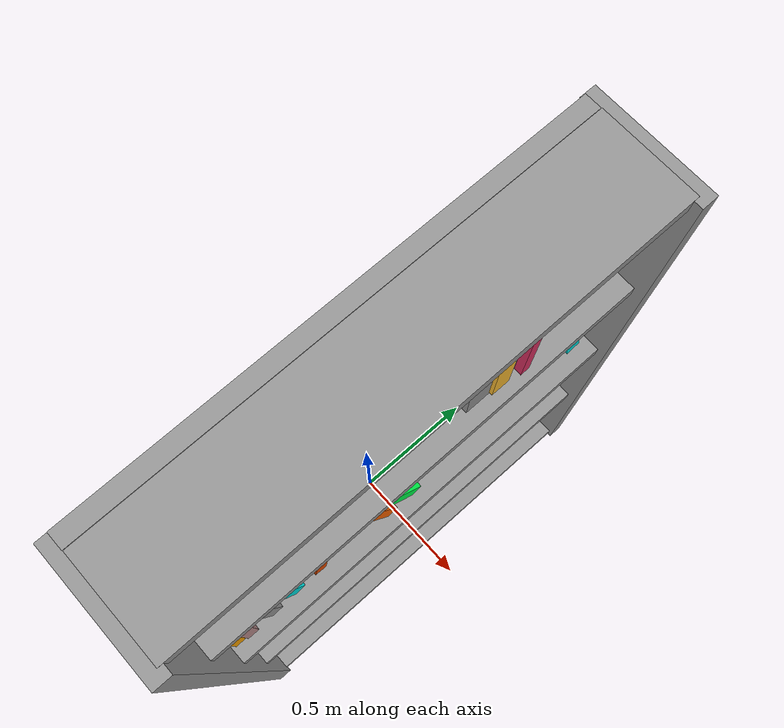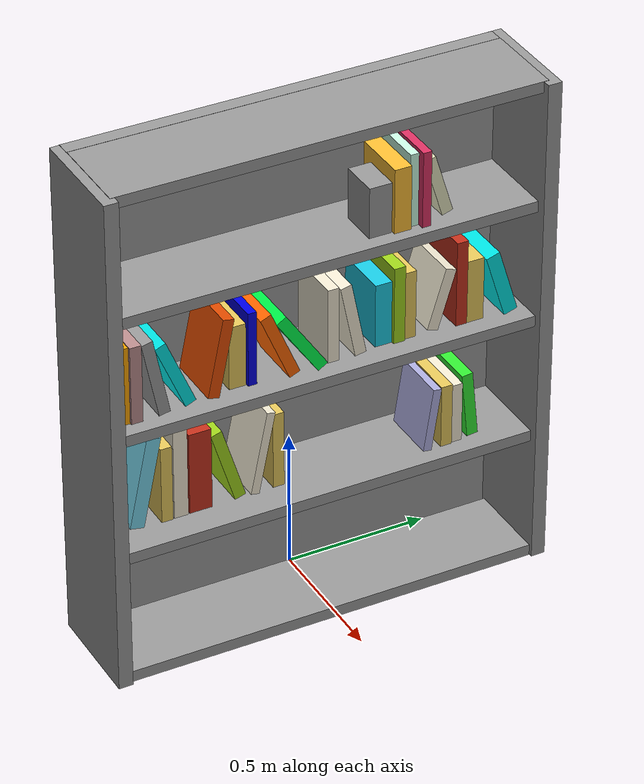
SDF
<?xml version='1.0'?>
<sdf version='1.7'>
  <model name='my_bookshelf'>
    <link name='link'>
      <inertial>
        <mass>1</mass>
        <inertia>
          <ixx>0.166667</ixx>
          <ixy>0</ixy>
          <ixz>0</ixz>
          <iyy>0.166667</iyy>
          <iyz>0</iyz>
          <izz>0.166667</izz>
        </inertia>
        <pose>0 0 0 0 -0 0</pose>
      </inertial>
      <self_collide>0</self_collide>
      <enable_wind>0</enable_wind>
      <kinematic>0</kinematic>
      <pose>0.010503 -0.018536 0.006993 0 -0 0</pose>
      <gravity>1</gravity>
      <visual name='visual'>
        <geometry>
          <box>
            <size>0.05 1.5 1.8</size>
          </box>
        </geometry>
        <material>
          <script>
            <name>Gazebo/Grey</name>
            <uri>file://media/materials/scripts/gazebo.material</uri>
          </script>
          <shader type='pixel'>
            <normal_map>__default__</normal_map>
          </shader>
          <ambient>0.9 0.9 0.9 1</ambient>
          <diffuse>0.9 0.9 0.9 1</diffuse>
          <specular>0.01 0.01 0.01 1</specular>
          <emissive>0 0 0 1</emissive>
        </material>
        <pose>0 0 0.9 0 -0 0</pose>
        <transparency>0</transparency>
        <cast_shadows>1</cast_shadows>
      </visual>
      <collision name='collision'>
        <laser_retro>0</laser_retro>
        <max_contacts>10</max_contacts>
        <pose>0 0 0.9 0 -0 0</pose>
        <geometry>
          <box>
            <size>0.05 1.5 1.8</size>
          </box>
        </geometry>
        <surface>
          <friction>
            <ode>
              <mu>1</mu>
              <mu2>1</mu2>
              <fdir1>0 0 0</fdir1>
              <slip1>0</slip1>
              <slip2>0</slip2>
            </ode>
            <torsional>
              <coefficient>1</coefficient>
              <patch_radius>0</patch_radius>
              <surface_radius>0</surface_radius>
              <use_patch_radius>1</use_patch_radius>
              <ode>
                <slip>0</slip>
              </ode>
            </torsional>
          </friction>
          <bounce>
            <restitution_coefficient>0</restitution_coefficient>
            <threshold>1e+06</threshold>
          </bounce>
          <contact>
            <collide_without_contact>0</collide_without_contact>
            <collide_without_contact_bitmask>1</collide_without_contact_bitmask>
            <collide_bitmask>1</collide_bitmask>
            <ode>
              <soft_cfm>0</soft_cfm>
              <soft_erp>0.2</soft_erp>
              <kp>1e+13</kp>
              <kd>1</kd>
              <max_vel>0.01</max_vel>
              <min_depth>0</min_depth>
            </ode>
            <bullet>
              <split_impulse>1</split_impulse>
              <split_impulse_penetration_threshold>-0.01</split_impulse_penetration_threshold>
              <soft_cfm>0</soft_cfm>
              <soft_erp>0.2</soft_erp>
              <kp>1e+13</kp>
              <kd>1</kd>
            </bullet>
          </contact>
        </surface>
      </collision>
    </link>
    <link name='link_0'>
      <inertial>
        <mass>1</mass>
        <inertia>
          <ixx>0.166667</ixx>
          <ixy>0</ixy>
          <ixz>0</ixz>
          <iyy>0.166667</iyy>
          <iyz>0</iyz>
          <izz>0.166667</izz>
        </inertia>
        <pose>0 0 0 0 -0 0</pose>
      </inertial>
      <pose>0.126439 -0.625111 0.659532 0 -0 0</pose>
      <gravity>0</gravity>
      <self_collide>0</self_collide>
      <kinematic>0</kinematic>
      <enable_wind>0</enable_wind>
      <visual name='visual'>
        <pose>0 0 0 -0.2 0 0</pose>
        <geometry>
          <box>
            <size>0.2 0.05 0.33</size>
          </box>
        </geometry>
        <material>
          <lighting>1</lighting>
          <script>
            <uri>file://media/materials/scripts/gazebo.material</uri>
            <name>Gazebo/Grey</name>
          </script>
          <shader type='pixel'>
            <normal_map>__default__</normal_map>
          </shader>
          <ambient>0.47 0.84 0.93 1</ambient>
          <diffuse>0.47 0.84 0.93 1</diffuse>
          <specular>0.01 0.01 0.01 1</specular>
          <emissive>0 0 0 1</emissive>
        </material>
        <transparency>0</transparency>
        <cast_shadows>1</cast_shadows>
      </visual>
      <collision name='collision'>
        <laser_retro>0</laser_retro>
        <max_contacts>10</max_contacts>
        <pose>0 0 0 -0.2 0 0</pose>
        <geometry>
          <box>
            <size>0.2 0.05 0.33</size>
          </box>
        </geometry>
        <surface>
          <friction>
            <ode>
              <mu>1</mu>
              <mu2>1</mu2>
              <fdir1>0 0 0</fdir1>
              <slip1>0</slip1>
              <slip2>0</slip2>
            </ode>
            <torsional>
              <coefficient>1</coefficient>
              <patch_radius>0</patch_radius>
              <surface_radius>0</surface_radius>
              <use_patch_radius>1</use_patch_radius>
              <ode>
                <slip>0</slip>
              </ode>
            </torsional>
          </friction>
          <bounce>
            <restitution_coefficient>0</restitution_coefficient>
            <threshold>1e+06</threshold>
          </bounce>
          <contact>
            <collide_without_contact>0</collide_without_contact>
            <collide_without_contact_bitmask>1</collide_without_contact_bitmask>
            <collide_bitmask>1</collide_bitmask>
            <ode>
              <soft_cfm>0</soft_cfm>
              <soft_erp>0.2</soft_erp>
              <kp>1e+13</kp>
              <kd>1</kd>
              <max_vel>0.01</max_vel>
              <min_depth>0</min_depth>
            </ode>
            <bullet>
              <split_impulse>1</split_impulse>
              <split_impulse_penetration_threshold>-0.01</split_impulse_penetration_threshold>
              <soft_cfm>0</soft_cfm>
              <soft_erp>0.2</soft_erp>
              <kp>1e+13</kp>
              <kd>1</kd>
            </bullet>
          </contact>
        </surface>
      </collision>
    </link>
    <link name='link_0_clone'>
      <inertial>
        <mass>1</mass>
        <inertia>
          <ixx>0.166667</ixx>
          <ixy>0</ixy>
          <ixz>0</ixz>
          <iyy>0.166667</iyy>
          <iyz>0</iyz>
          <izz>0.166667</izz>
        </inertia>
        <pose>0 0 0 0 -0 0</pose>
      </inertial>
      <pose>0.132216 -0.554276 0.635683 0 -0 0</pose>
      <gravity>1</gravity>
      <self_collide>0</self_collide>
      <kinematic>0</kinematic>
      <enable_wind>0</enable_wind>
      <visual name='visual'>
        <pose>0 0 0 0 -0 0</pose>
        <geometry>
          <box>
            <size>0.2 0.04 0.28</size>
          </box>
        </geometry>
        <material>
          <lighting>1</lighting>
          <script>
            <uri>file://media/materials/scripts/gazebo.material</uri>
            <name>Gazebo/Grey</name>
          </script>
          <shader type='pixel'>
            <normal_map>__default__</normal_map>
          </shader>
          <ambient>0.91 0.79 0.36 1</ambient>
          <diffuse>0.91 0.79 0.36 1</diffuse>
          <specular>0.01 0.01 0.01 1</specular>
          <emissive>0 0 0 1</emissive>
        </material>
        <transparency>0</transparency>
        <cast_shadows>1</cast_shadows>
      </visual>
      <collision name='collision'>
        <laser_retro>0</laser_retro>
        <max_contacts>10</max_contacts>
        <pose>0 0 0 0 -0 0</pose>
        <geometry>
          <box>
            <size>0.2 0.04 0.28</size>
          </box>
        </geometry>
        <surface>
          <friction>
            <ode>
              <mu>1</mu>
              <mu2>1</mu2>
              <fdir1>0 0 0</fdir1>
              <slip1>0</slip1>
              <slip2>0</slip2>
            </ode>
            <torsional>
              <coefficient>1</coefficient>
              <patch_radius>0</patch_radius>
              <surface_radius>0</surface_radius>
              <use_patch_radius>1</use_patch_radius>
              <ode>
                <slip>0</slip>
              </ode>
            </torsional>
          </friction>
          <bounce>
            <restitution_coefficient>0</restitution_coefficient>
            <threshold>1e+06</threshold>
          </bounce>
          <contact>
            <collide_without_contact>0</collide_without_contact>
            <collide_without_contact_bitmask>1</collide_without_contact_bitmask>
            <collide_bitmask>1</collide_bitmask>
            <ode>
              <soft_cfm>0</soft_cfm>
              <soft_erp>0.2</soft_erp>
              <kp>1e+13</kp>
              <kd>1</kd>
              <max_vel>0.01</max_vel>
              <min_depth>0</min_depth>
            </ode>
            <bullet>
              <split_impulse>1</split_impulse>
              <split_impulse_penetration_threshold>-0.01</split_impulse_penetration_threshold>
              <soft_cfm>0</soft_cfm>
              <soft_erp>0.2</soft_erp>
              <kp>1e+13</kp>
              <kd>1</kd>
            </bullet>
          </contact>
        </surface>
      </collision>
    </link>
    <link name='link_0_clone_0'>
      <inertial>
        <mass>1</mass>
        <inertia>
          <ixx>0.166667</ixx>
          <ixy>0</ixy>
          <ixz>0</ixz>
          <iyy>0.166667</iyy>
          <iyz>0</iyz>
          <izz>0.166667</izz>
        </inertia>
        <pose>0 0 0 0 -0 0</pose>
      </inertial>
      <pose>0.128809 -0.503591 0.659532 0 -0 0</pose>
      <gravity>1</gravity>
      <self_collide>0</self_collide>
      <kinematic>0</kinematic>
      <enable_wind>0</enable_wind>
      <visual name='visual'>
        <pose>0 0 0 0 -0 0</pose>
        <geometry>
          <box>
            <size>0.2 0.05 0.33</size>
          </box>
        </geometry>
        <material>
          <lighting>1</lighting>
          <script>
            <uri>file://media/materials/scripts/gazebo.material</uri>
            <name>Gazebo/Grey</name>
          </script>
          <shader type='pixel'>
            <normal_map>__default__</normal_map>
          </shader>
          <ambient>0.96 0.93 0.84 1</ambient>
          <diffuse>0.96 0.93 0.84 1</diffuse>
          <specular>0.01 0.01 0.01 1</specular>
          <emissive>0 0 0 1</emissive>
        </material>
        <transparency>0</transparency>
        <cast_shadows>1</cast_shadows>
      </visual>
      <collision name='collision'>
        <laser_retro>0</laser_retro>
        <max_contacts>10</max_contacts>
        <pose>0 0 0 0 -0 0</pose>
        <geometry>
          <box>
            <size>0.2 0.05 0.33</size>
          </box>
        </geometry>
        <surface>
          <friction>
            <ode>
              <mu>1</mu>
              <mu2>1</mu2>
              <fdir1>0 0 0</fdir1>
              <slip1>0</slip1>
              <slip2>0</slip2>
            </ode>
            <torsional>
              <coefficient>1</coefficient>
              <patch_radius>0</patch_radius>
              <surface_radius>0</surface_radius>
              <use_patch_radius>1</use_patch_radius>
              <ode>
                <slip>0</slip>
              </ode>
            </torsional>
          </friction>
          <bounce>
            <restitution_coefficient>0</restitution_coefficient>
            <threshold>1e+06</threshold>
          </bounce>
          <contact>
            <collide_without_contact>0</collide_without_contact>
            <collide_without_contact_bitmask>1</collide_without_contact_bitmask>
            <collide_bitmask>1</collide_bitmask>
            <ode>
              <soft_cfm>0</soft_cfm>
              <soft_erp>0.2</soft_erp>
              <kp>1e+13</kp>
              <kd>1</kd>
              <max_vel>0.01</max_vel>
              <min_depth>0</min_depth>
            </ode>
            <bullet>
              <split_impulse>1</split_impulse>
              <split_impulse_penetration_threshold>-0.01</split_impulse_penetration_threshold>
              <soft_cfm>0</soft_cfm>
              <soft_erp>0.2</soft_erp>
              <kp>1e+13</kp>
              <kd>1</kd>
            </bullet>
          </contact>
        </surface>
      </collision>
    </link>
    <link name='link_0_clone_0_clone'>
      <inertial>
        <mass>1</mass>
        <inertia>
          <ixx>0.166667</ixx>
          <ixy>0</ixy>
          <ixz>0</ixz>
          <iyy>0.166667</iyy>
          <iyz>0</iyz>
          <izz>0.166667</izz>
        </inertia>
        <pose>0 0 0 0 -0 0</pose>
      </inertial>
      <pose>0.130424 -0.435023 0.647115 0 -0 0</pose>
      <gravity>1</gravity>
      <self_collide>0</self_collide>
      <kinematic>0</kinematic>
      <enable_wind>0</enable_wind>
      <visual name='visual'>
        <pose>0 0 0 0 -0 0</pose>
        <geometry>
          <box>
            <size>0.2 0.08 0.3</size>
          </box>
        </geometry>
        <material>
          <lighting>1</lighting>
          <script>
            <uri>file://media/materials/scripts/gazebo.material</uri>
            <name>Gazebo/Grey</name>
          </script>
          <shader type='pixel'>
            <normal_map>__default__</normal_map>
          </shader>
          <ambient>0.78 0.19 0.11 1</ambient>
          <diffuse>0.78 0.19 0.11 1</diffuse>
          <specular>0.01 0.01 0.01 1</specular>
          <emissive>0 0 0 1</emissive>
        </material>
        <transparency>0</transparency>
        <cast_shadows>1</cast_shadows>
      </visual>
      <collision name='collision'>
        <laser_retro>0</laser_retro>
        <max_contacts>10</max_contacts>
        <pose>0 0 0 0 -0 0</pose>
        <geometry>
          <box>
            <size>0.2 0.08 0.3</size>
          </box>
        </geometry>
        <surface>
          <friction>
            <ode>
              <mu>1</mu>
              <mu2>1</mu2>
              <fdir1>0 0 0</fdir1>
              <slip1>0</slip1>
              <slip2>0</slip2>
            </ode>
            <torsional>
              <coefficient>1</coefficient>
              <patch_radius>0</patch_radius>
              <surface_radius>0</surface_radius>
              <use_patch_radius>1</use_patch_radius>
              <ode>
                <slip>0</slip>
              </ode>
            </torsional>
          </friction>
          <bounce>
            <restitution_coefficient>0</restitution_coefficient>
            <threshold>1e+06</threshold>
          </bounce>
          <contact>
            <collide_without_contact>0</collide_without_contact>
            <collide_without_contact_bitmask>1</collide_without_contact_bitmask>
            <collide_bitmask>1</collide_bitmask>
            <ode>
              <soft_cfm>0</soft_cfm>
              <soft_erp>0.2</soft_erp>
              <kp>1e+13</kp>
              <kd>1</kd>
              <max_vel>0.01</max_vel>
              <min_depth>0</min_depth>
            </ode>
            <bullet>
              <split_impulse>1</split_impulse>
              <split_impulse_penetration_threshold>-0.01</split_impulse_penetration_threshold>
              <soft_cfm>0</soft_cfm>
              <soft_erp>0.2</soft_erp>
              <kp>1e+13</kp>
              <kd>1</kd>
            </bullet>
          </contact>
        </surface>
      </collision>
    </link>
    <link name='link_0_clone_0_clone_0'>
      <inertial>
        <mass>1</mass>
        <inertia>
          <ixx>0.166667</ixx>
          <ixy>0</ixy>
          <ixz>0</ixz>
          <iyy>0.166667</iyy>
          <iyz>0</iyz>
          <izz>0.166667</izz>
        </inertia>
        <pose>0 0 0 0 -0 0</pose>
      </inertial>
      <pose>0.13743 -0.21618 0.64809 0 -0 0</pose>
      <gravity>0</gravity>
      <self_collide>0</self_collide>
      <kinematic>0</kinematic>
      <enable_wind>0</enable_wind>
      <visual name='visual'>
        <pose>0 0 0 -0.2 0 0</pose>
        <geometry>
          <box>
            <size>0.2 0.03 0.3</size>
          </box>
        </geometry>
        <material>
          <lighting>1</lighting>
          <script>
            <uri>file://media/materials/scripts/gazebo.material</uri>
            <name>Gazebo/Grey</name>
          </script>
          <shader type='pixel'>
            <normal_map>__default__</normal_map>
          </shader>
          <ambient>0.96 0.93 0.84 1</ambient>
          <diffuse>0.96 0.93 0.84 1</diffuse>
          <specular>0.01 0.01 0.01 1</specular>
          <emissive>0 0 0 1</emissive>
        </material>
        <transparency>0</transparency>
        <cast_shadows>1</cast_shadows>
      </visual>
      <collision name='collision'>
        <laser_retro>0</laser_retro>
        <max_contacts>10</max_contacts>
        <pose>0 0 0 -0.2 0 0</pose>
        <geometry>
          <box>
            <size>0.2 0.03 0.3</size>
          </box>
        </geometry>
        <surface>
          <friction>
            <ode>
              <mu>1</mu>
              <mu2>1</mu2>
              <fdir1>0 0 0</fdir1>
              <slip1>0</slip1>
              <slip2>0</slip2>
            </ode>
            <torsional>
              <coefficient>1</coefficient>
              <patch_radius>0</patch_radius>
              <surface_radius>0</surface_radius>
              <use_patch_radius>1</use_patch_radius>
              <ode>
                <slip>0</slip>
              </ode>
            </torsional>
          </friction>
          <bounce>
            <restitution_coefficient>0</restitution_coefficient>
            <threshold>1e+06</threshold>
          </bounce>
          <contact>
            <collide_without_contact>0</collide_without_contact>
            <collide_without_contact_bitmask>1</collide_without_contact_bitmask>
            <collide_bitmask>1</collide_bitmask>
            <ode>
              <soft_cfm>0</soft_cfm>
              <soft_erp>0.2</soft_erp>
              <kp>1e+13</kp>
              <kd>1</kd>
              <max_vel>0.01</max_vel>
              <min_depth>0</min_depth>
            </ode>
            <bullet>
              <split_impulse>1</split_impulse>
              <split_impulse_penetration_threshold>-0.01</split_impulse_penetration_threshold>
              <soft_cfm>0</soft_cfm>
              <soft_erp>0.2</soft_erp>
              <kp>1e+13</kp>
              <kd>1</kd>
            </bullet>
          </contact>
        </surface>
      </collision>
    </link>
    <link name='link_0_clone_0_clone_1'>
      <inertial>
        <mass>1</mass>
        <inertia>
          <ixx>0.166667</ixx>
          <ixy>0</ixy>
          <ixz>0</ixz>
          <iyy>0.166667</iyy>
          <iyz>0</iyz>
          <izz>0.166667</izz>
        </inertia>
        <pose>0 0 0 0 -0 0</pose>
      </inertial>
      <pose>0.167852 0.018542 1.07916 0 -0 0</pose>
      <gravity>1</gravity>
      <self_collide>0</self_collide>
      <kinematic>0</kinematic>
      <enable_wind>0</enable_wind>
      <visual name='visual'>
        <pose>0 0 0 0 -0 0</pose>
        <geometry>
          <box>
            <size>0.2 0.04 0.27</size>
          </box>
        </geometry>
        <material>
          <lighting>1</lighting>
          <script>
            <uri>file://media/materials/scripts/gazebo.material</uri>
            <name>Gazebo/Grey</name>
          </script>
          <shader type='pixel'>
            <normal_map>__default__</normal_map>
          </shader>
          <ambient>0.96 0.93 0.84 1</ambient>
          <diffuse>0.96 0.93 0.84 1</diffuse>
          <specular>0.01 0.01 0.01 1</specular>
          <emissive>0 0 0 1</emissive>
        </material>
        <transparency>0</transparency>
        <cast_shadows>1</cast_shadows>
      </visual>
      <collision name='collision'>
        <laser_retro>0</laser_retro>
        <max_contacts>10</max_contacts>
        <pose>0 0 0 0 -0 0</pose>
        <geometry>
          <box>
            <size>0.2 0.04 0.27</size>
          </box>
        </geometry>
        <surface>
          <friction>
            <ode>
              <mu>1</mu>
              <mu2>1</mu2>
              <fdir1>0 0 0</fdir1>
              <slip1>0</slip1>
              <slip2>0</slip2>
            </ode>
            <torsional>
              <coefficient>1</coefficient>
              <patch_radius>0</patch_radius>
              <surface_radius>0</surface_radius>
              <use_patch_radius>1</use_patch_radius>
              <ode>
                <slip>0</slip>
              </ode>
            </torsional>
          </friction>
          <bounce>
            <restitution_coefficient>0</restitution_coefficient>
            <threshold>1e+06</threshold>
          </bounce>
          <contact>
            <collide_without_contact>0</collide_without_contact>
            <collide_without_contact_bitmask>1</collide_without_contact_bitmask>
            <collide_bitmask>1</collide_bitmask>
            <ode>
              <soft_cfm>0</soft_cfm>
              <soft_erp>0.2</soft_erp>
              <kp>1e+13</kp>
              <kd>1</kd>
              <max_vel>0.01</max_vel>
              <min_depth>0</min_depth>
            </ode>
            <bullet>
              <split_impulse>1</split_impulse>
              <split_impulse_penetration_threshold>-0.01</split_impulse_penetration_threshold>
              <soft_cfm>0</soft_cfm>
              <soft_erp>0.2</soft_erp>
              <kp>1e+13</kp>
              <kd>1</kd>
            </bullet>
          </contact>
        </surface>
      </collision>
    </link>
    <link name='link_0_clone_0_clone_1_clone'>
      <inertial>
        <mass>1</mass>
        <inertia>
          <ixx>0.166667</ixx>
          <ixy>0</ixy>
          <ixz>0</ixz>
          <iyy>0.166667</iyy>
          <iyz>0</iyz>
          <izz>0.166667</izz>
        </inertia>
        <pose>0 0 0 0 -0 0</pose>
      </inertial>
      <pose>0.171551 0.087441 1.07916 0 -0 0</pose>
      <gravity>1</gravity>
      <self_collide>0</self_collide>
      <kinematic>0</kinematic>
      <enable_wind>0</enable_wind>
      <visual name='visual'>
        <pose>0 0 0 0.2 -0 0</pose>
        <geometry>
          <box>
            <size>0.2 0.04 0.27</size>
          </box>
        </geometry>
        <material>
          <lighting>1</lighting>
          <script>
            <uri>file://media/materials/scripts/gazebo.material</uri>
            <name>Gazebo/Grey</name>
          </script>
          <shader type='pixel'>
            <normal_map>__default__</normal_map>
          </shader>
          <ambient>0.96 0 0 1</ambient>
          <diffuse>0.96 0.93 0.84 1</diffuse>
          <specular>0.01 0.01 0.01 1</specular>
          <emissive>0 0 0 1</emissive>
        </material>
        <transparency>0</transparency>
        <cast_shadows>1</cast_shadows>
      </visual>
      <collision name='collision'>
        <laser_retro>0</laser_retro>
        <max_contacts>10</max_contacts>
        <pose>0 0 0 0.2 -0 0</pose>
        <geometry>
          <box>
            <size>0.2 0.04 0.27</size>
          </box>
        </geometry>
        <surface>
          <friction>
            <ode>
              <mu>1</mu>
              <mu2>1</mu2>
              <fdir1>0 0 0</fdir1>
              <slip1>0</slip1>
              <slip2>0</slip2>
            </ode>
            <torsional>
              <coefficient>1</coefficient>
              <patch_radius>0</patch_radius>
              <surface_radius>0</surface_radius>
              <use_patch_radius>1</use_patch_radius>
              <ode>
                <slip>0</slip>
              </ode>
            </torsional>
          </friction>
          <bounce>
            <restitution_coefficient>0</restitution_coefficient>
            <threshold>1e+06</threshold>
          </bounce>
          <contact>
            <collide_without_contact>0</collide_without_contact>
            <collide_without_contact_bitmask>1</collide_without_contact_bitmask>
            <collide_bitmask>1</collide_bitmask>
            <ode>
              <soft_cfm>0</soft_cfm>
              <soft_erp>0.2</soft_erp>
              <kp>1e+13</kp>
              <kd>1</kd>
              <max_vel>0.01</max_vel>
              <min_depth>0</min_depth>
            </ode>
            <bullet>
              <split_impulse>1</split_impulse>
              <split_impulse_penetration_threshold>-0.01</split_impulse_penetration_threshold>
              <soft_cfm>0</soft_cfm>
              <soft_erp>0.2</soft_erp>
              <kp>1e+13</kp>
              <kd>1</kd>
            </bullet>
          </contact>
        </surface>
      </collision>
    </link>
    <link name='link_0_clone_0_clone_1_clone_0'>
      <inertial>
        <mass>1</mass>
        <inertia>
          <ixx>0.166667</ixx>
          <ixy>0</ixy>
          <ixz>0</ixz>
          <iyy>0.166667</iyy>
          <iyz>0</iyz>
          <izz>0.166667</izz>
        </inertia>
        <pose>0 0 0 0 -0 0</pose>
      </inertial>
      <pose>0.163095 0.41037 1.0549 0 -0 0</pose>
      <gravity>1</gravity>
      <self_collide>0</self_collide>
      <kinematic>0</kinematic>
      <enable_wind>0</enable_wind>
      <visual name='visual'>
        <pose>0 0 0 -0.3 0 0</pose>
        <geometry>
          <box>
            <size>0.2 0.04 0.22</size>
          </box>
        </geometry>
        <material>
          <lighting>1</lighting>
          <script>
            <uri>file://media/materials/scripts/gazebo.material</uri>
            <name>Gazebo/Grey</name>
          </script>
          <shader type='pixel'>
            <normal_map>__default__</normal_map>
          </shader>
          <ambient>0.96 0.93 0.84 1</ambient>
          <diffuse>0.96 0.93 0.84 1</diffuse>
          <specular>0.01 0.01 0.01 1</specular>
          <emissive>0 0 0 1</emissive>
        </material>
        <transparency>0</transparency>
        <cast_shadows>1</cast_shadows>
      </visual>
      <collision name='collision'>
        <laser_retro>0</laser_retro>
        <max_contacts>10</max_contacts>
        <pose>0 0 0 -0.3 0 0</pose>
        <geometry>
          <box>
            <size>0.2 0.04 0.22</size>
          </box>
        </geometry>
        <surface>
          <friction>
            <ode>
              <mu>1</mu>
              <mu2>1</mu2>
              <fdir1>0 0 0</fdir1>
              <slip1>0</slip1>
              <slip2>0</slip2>
            </ode>
            <torsional>
              <coefficient>1</coefficient>
              <patch_radius>0</patch_radius>
              <surface_radius>0</surface_radius>
              <use_patch_radius>1</use_patch_radius>
              <ode>
                <slip>0</slip>
              </ode>
            </torsional>
          </friction>
          <bounce>
            <restitution_coefficient>0</restitution_coefficient>
            <threshold>1e+06</threshold>
          </bounce>
          <contact>
            <collide_without_contact>0</collide_without_contact>
            <collide_without_contact_bitmask>1</collide_without_contact_bitmask>
            <collide_bitmask>1</collide_bitmask>
            <ode>
              <soft_cfm>0</soft_cfm>
              <soft_erp>0.2</soft_erp>
              <kp>1e+13</kp>
              <kd>1</kd>
              <max_vel>0.01</max_vel>
              <min_depth>0</min_depth>
            </ode>
            <bullet>
              <split_impulse>1</split_impulse>
              <split_impulse_penetration_threshold>-0.01</split_impulse_penetration_threshold>
              <soft_cfm>0</soft_cfm>
              <soft_erp>0.2</soft_erp>
              <kp>1e+13</kp>
              <kd>1</kd>
            </bullet>
          </contact>
        </surface>
      </collision>
    </link>
    <link name='link_0_clone_0_clone_1_clone_0_clone'>
      <inertial>
        <mass>1</mass>
        <inertia>
          <ixx>0.166667</ixx>
          <ixy>0</ixy>
          <ixz>0</ixz>
          <iyy>0.166667</iyy>
          <iyz>0</iyz>
          <izz>0.166667</izz>
        </inertia>
        <pose>0 0 0 0 -0 0</pose>
      </inertial>
      <pose>0.169255 0.470698 0.604493 0 -0 0</pose>
      <gravity>1</gravity>
      <self_collide>0</self_collide>
      <kinematic>0</kinematic>
      <enable_wind>0</enable_wind>
      <visual name='visual'>
        <pose>0 0 0 0 -0 0</pose>
        <geometry>
          <box>
            <size>0.2 0.04 0.22</size>
          </box>
        </geometry>
        <material>
          <lighting>1</lighting>
          <script>
            <uri>file://media/materials/scripts/gazebo.material</uri>
            <name>Gazebo/Grey</name>
          </script>
          <shader type='pixel'>
            <normal_map>__default__</normal_map>
          </shader>
          <ambient>0.96 0.93 0.84 1</ambient>
          <diffuse>0.96 0.93 0.84 1</diffuse>
          <specular>0.01 0.01 0.01 1</specular>
          <emissive>0 0 0 1</emissive>
        </material>
        <transparency>0</transparency>
        <cast_shadows>1</cast_shadows>
      </visual>
      <collision name='collision'>
        <laser_retro>0</laser_retro>
        <max_contacts>10</max_contacts>
        <pose>0 0 0 0 -0 0</pose>
        <geometry>
          <box>
            <size>0.2 0.04 0.22</size>
          </box>
        </geometry>
        <surface>
          <friction>
            <ode>
              <mu>1</mu>
              <mu2>1</mu2>
              <fdir1>0 0 0</fdir1>
              <slip1>0</slip1>
              <slip2>0</slip2>
            </ode>
            <torsional>
              <coefficient>1</coefficient>
              <patch_radius>0</patch_radius>
              <surface_radius>0</surface_radius>
              <use_patch_radius>1</use_patch_radius>
              <ode>
                <slip>0</slip>
              </ode>
            </torsional>
          </friction>
          <bounce>
            <restitution_coefficient>0</restitution_coefficient>
            <threshold>1e+06</threshold>
          </bounce>
          <contact>
            <collide_without_contact>0</collide_without_contact>
            <collide_without_contact_bitmask>1</collide_without_contact_bitmask>
            <collide_bitmask>1</collide_bitmask>
            <ode>
              <soft_cfm>0</soft_cfm>
              <soft_erp>0.2</soft_erp>
              <kp>1e+13</kp>
              <kd>1</kd>
              <max_vel>0.01</max_vel>
              <min_depth>0</min_depth>
            </ode>
            <bullet>
              <split_impulse>1</split_impulse>
              <split_impulse_penetration_threshold>-0.01</split_impulse_penetration_threshold>
              <soft_cfm>0</soft_cfm>
              <soft_erp>0.2</soft_erp>
              <kp>1e+13</kp>
              <kd>1</kd>
            </bullet>
          </contact>
        </surface>
      </collision>
    </link>
    <link name='link_0_clone_0_clone_1_clone_0_clone_0'>
      <inertial>
        <mass>1</mass>
        <inertia>
          <ixx>0.166667</ixx>
          <ixy>0</ixy>
          <ixz>0</ixz>
          <iyy>0.166667</iyy>
          <iyz>0</iyz>
          <izz>0.166667</izz>
        </inertia>
        <pose>0 0 0 0 -0 0</pose>
      </inertial>
      <pose>0.160366 0.392824 1.48014 0 -0 0</pose>
      <gravity>1</gravity>
      <self_collide>0</self_collide>
      <kinematic>0</kinematic>
      <enable_wind>0</enable_wind>
      <visual name='visual'>
        <pose>0 0 0 0.3 -0 0</pose>
        <geometry>
          <box>
            <size>0.2 0.04 0.22</size>
          </box>
        </geometry>
        <material>
          <lighting>1</lighting>
          <script>
            <uri>file://media/materials/scripts/gazebo.material</uri>
            <name>Gazebo/Grey</name>
          </script>
          <shader type='pixel'>
            <normal_map>__default__</normal_map>
          </shader>
          <ambient>0.9 0.9 0.75 1</ambient>
          <diffuse>0.9 0.9 0.75 1</diffuse>
          <specular>0.01 0.01 0.01 1</specular>
          <emissive>0 0 0 1</emissive>
        </material>
        <transparency>0</transparency>
        <cast_shadows>1</cast_shadows>
      </visual>
      <collision name='collision'>
        <laser_retro>0</laser_retro>
        <max_contacts>10</max_contacts>
        <pose>0 0 0 0.3 -0 0</pose>
        <geometry>
          <box>
            <size>0.2 0.04 0.22</size>
          </box>
        </geometry>
        <surface>
          <friction>
            <ode>
              <mu>1</mu>
              <mu2>1</mu2>
              <fdir1>0 0 0</fdir1>
              <slip1>0</slip1>
              <slip2>0</slip2>
            </ode>
            <torsional>
              <coefficient>1</coefficient>
              <patch_radius>0</patch_radius>
              <surface_radius>0</surface_radius>
              <use_patch_radius>1</use_patch_radius>
              <ode>
                <slip>0</slip>
              </ode>
            </torsional>
          </friction>
          <bounce>
            <restitution_coefficient>0</restitution_coefficient>
            <threshold>1e+06</threshold>
          </bounce>
          <contact>
            <collide_without_contact>0</collide_without_contact>
            <collide_without_contact_bitmask>1</collide_without_contact_bitmask>
            <collide_bitmask>1</collide_bitmask>
            <ode>
              <soft_cfm>0</soft_cfm>
              <soft_erp>0.2</soft_erp>
              <kp>1e+13</kp>
              <kd>1</kd>
              <max_vel>0.01</max_vel>
              <min_depth>0</min_depth>
            </ode>
            <bullet>
              <split_impulse>1</split_impulse>
              <split_impulse_penetration_threshold>-0.01</split_impulse_penetration_threshold>
              <soft_cfm>0</soft_cfm>
              <soft_erp>0.2</soft_erp>
              <kp>1e+13</kp>
              <kd>1</kd>
            </bullet>
          </contact>
        </surface>
      </collision>
    </link>
    <link name='link_0_clone_0_clone_1_clone_0_clone_clone'>
      <inertial>
        <mass>1</mass>
        <inertia>
          <ixx>0.166667</ixx>
          <ixy>0</ixy>
          <ixz>0</ixz>
          <iyy>0.166667</iyy>
          <iyz>0</iyz>
          <izz>0.166667</izz>
        </inertia>
        <pose>0 0 0 0 -0 0</pose>
      </inertial>
      <pose>0.161553 0.523575 0.616111 0 -0 0</pose>
      <gravity>1</gravity>
      <self_collide>0</self_collide>
      <kinematic>0</kinematic>
      <enable_wind>0</enable_wind>
      <visual name='visual'>
        <pose>0 0 0 0.1 -0 0</pose>
        <geometry>
          <box>
            <size>0.2 0.04 0.24</size>
          </box>
        </geometry>
        <material>
          <lighting>1</lighting>
          <script>
            <uri>file://media/materials/scripts/gazebo.material</uri>
            <name>Gazebo/Grey</name>
          </script>
          <shader type='pixel'>
            <normal_map>__default__</normal_map>
          </shader>
          <ambient>0.2 0.93 0.2 1</ambient>
          <diffuse>0.2 0.93 0.2 1</diffuse>
          <specular>0.01 0.01 0.01 1</specular>
          <emissive>0 0 0 1</emissive>
        </material>
        <transparency>0</transparency>
        <cast_shadows>1</cast_shadows>
      </visual>
      <collision name='collision'>
        <laser_retro>0</laser_retro>
        <max_contacts>10</max_contacts>
        <pose>0 0 0 0.1 -0 0</pose>
        <geometry>
          <box>
            <size>0.2 0.04 0.24</size>
          </box>
        </geometry>
        <surface>
          <friction>
            <ode>
              <mu>1</mu>
              <mu2>1</mu2>
              <fdir1>0 0 0</fdir1>
              <slip1>0</slip1>
              <slip2>0</slip2>
            </ode>
            <torsional>
              <coefficient>1</coefficient>
              <patch_radius>0</patch_radius>
              <surface_radius>0</surface_radius>
              <use_patch_radius>1</use_patch_radius>
              <ode>
                <slip>0</slip>
              </ode>
            </torsional>
          </friction>
          <bounce>
            <restitution_coefficient>0</restitution_coefficient>
            <threshold>1e+06</threshold>
          </bounce>
          <contact>
            <collide_without_contact>0</collide_without_contact>
            <collide_without_contact_bitmask>1</collide_without_contact_bitmask>
            <collide_bitmask>1</collide_bitmask>
            <ode>
              <soft_cfm>0</soft_cfm>
              <soft_erp>0.2</soft_erp>
              <kp>1e+13</kp>
              <kd>1</kd>
              <max_vel>0.01</max_vel>
              <min_depth>0</min_depth>
            </ode>
            <bullet>
              <split_impulse>1</split_impulse>
              <split_impulse_penetration_threshold>-0.01</split_impulse_penetration_threshold>
              <soft_cfm>0</soft_cfm>
              <soft_erp>0.2</soft_erp>
              <kp>1e+13</kp>
              <kd>1</kd>
            </bullet>
          </contact>
        </surface>
      </collision>
    </link>
    <link name='link_0_clone_0_clone_1_clone_1'>
      <inertial>
        <mass>1</mass>
        <inertia>
          <ixx>0.166667</ixx>
          <ixy>0</ixy>
          <ixz>0</ixz>
          <iyy>0.166667</iyy>
          <iyz>0</iyz>
          <izz>0.166667</izz>
        </inertia>
        <pose>0 0 0 0 -0 0</pose>
      </inertial>
      <pose>0.212864 0.174398 1.46448 0 -0 0</pose>
      <gravity>1</gravity>
      <self_collide>0</self_collide>
      <kinematic>0</kinematic>
      <enable_wind>0</enable_wind>
      <visual name='visual'>
        <pose>0 0 0 0 -0 0</pose>
        <geometry>
          <box>
            <size>0.14 0.08 0.18</size>
          </box>
        </geometry>
        <material>
          <lighting>1</lighting>
          <script>
            <uri>file://media/materials/scripts/gazebo.material</uri>
            <name>Gazebo/Grey</name>
          </script>
          <shader type='pixel'>
            <normal_map>__default__</normal_map>
          </shader>
          <ambient>0.945 0.95 0.95 1</ambient>
          <diffuse>0.94 0.95 0.95 1</diffuse>
          <specular>0.01 0.01 0.01 1</specular>
          <emissive>0 0 0 1</emissive>
        </material>
        <transparency>0</transparency>
        <cast_shadows>1</cast_shadows>
      </visual>
      <collision name='collision'>
        <laser_retro>0</laser_retro>
        <max_contacts>10</max_contacts>
        <pose>0 0 0 0 -0 0</pose>
        <geometry>
          <box>
            <size>0.14 0.08 0.18</size>
          </box>
        </geometry>
        <surface>
          <friction>
            <ode>
              <mu>1</mu>
              <mu2>1</mu2>
              <fdir1>0 0 0</fdir1>
              <slip1>0</slip1>
              <slip2>0</slip2>
            </ode>
            <torsional>
              <coefficient>1</coefficient>
              <patch_radius>0</patch_radius>
              <surface_radius>0</surface_radius>
              <use_patch_radius>1</use_patch_radius>
              <ode>
                <slip>0</slip>
              </ode>
            </torsional>
          </friction>
          <bounce>
            <restitution_coefficient>0</restitution_coefficient>
            <threshold>1e+06</threshold>
          </bounce>
          <contact>
            <collide_without_contact>0</collide_without_contact>
            <collide_without_contact_bitmask>1</collide_without_contact_bitmask>
            <collide_bitmask>1</collide_bitmask>
            <ode>
              <soft_cfm>0</soft_cfm>
              <soft_erp>0.2</soft_erp>
              <kp>1e+13</kp>
              <kd>1</kd>
              <max_vel>0.01</max_vel>
              <min_depth>0</min_depth>
            </ode>
            <bullet>
              <split_impulse>1</split_impulse>
              <split_impulse_penetration_threshold>-0.01</split_impulse_penetration_threshold>
              <soft_cfm>0</soft_cfm>
              <soft_erp>0.2</soft_erp>
              <kp>1e+13</kp>
              <kd>1</kd>
            </bullet>
          </contact>
        </surface>
      </collision>
    </link>
    <link name='link_0_clone_0_clone_clone'>
      <inertial>
        <mass>1</mass>
        <inertia>
          <ixx>0.166667</ixx>
          <ixy>0</ixy>
          <ixz>0</ixz>
          <iyy>0.166667</iyy>
          <iyz>0</iyz>
          <izz>0.166667</izz>
        </inertia>
        <pose>0 0 0 0 -0 0</pose>
      </inertial>
      <pose>0.167708 0.480351 1.09699 0 -0 0</pose>
      <gravity>1</gravity>
      <self_collide>0</self_collide>
      <kinematic>0</kinematic>
      <enable_wind>0</enable_wind>
      <visual name='visual'>
        <pose>0 0 0 0 -0 0</pose>
        <geometry>
          <box>
            <size>0.2 0.04 0.31</size>
          </box>
        </geometry>
        <material>
          <lighting>1</lighting>
          <script>
            <uri>file://media/materials/scripts/gazebo.material</uri>
            <name>Gazebo/Grey</name>
          </script>
          <shader type='pixel'>
            <normal_map>__default__</normal_map>
          </shader>
          <ambient>0.78 0.19 0.11 1</ambient>
          <diffuse>0.78 0.19 0.11 1</diffuse>
          <specular>0.01 0.01 0.01 1</specular>
          <emissive>0 0 0 1</emissive>
        </material>
        <transparency>0</transparency>
        <cast_shadows>1</cast_shadows>
      </visual>
      <collision name='collision'>
        <laser_retro>0</laser_retro>
        <max_contacts>10</max_contacts>
        <pose>0 0 0 0 -0 0</pose>
        <geometry>
          <box>
            <size>0.2 0.04 0.31</size>
          </box>
        </geometry>
        <surface>
          <friction>
            <ode>
              <mu>1</mu>
              <mu2>1</mu2>
              <fdir1>0 0 0</fdir1>
              <slip1>0</slip1>
              <slip2>0</slip2>
            </ode>
            <torsional>
              <coefficient>1</coefficient>
              <patch_radius>0</patch_radius>
              <surface_radius>0</surface_radius>
              <use_patch_radius>1</use_patch_radius>
              <ode>
                <slip>0</slip>
              </ode>
            </torsional>
          </friction>
          <bounce>
            <restitution_coefficient>0</restitution_coefficient>
            <threshold>1e+06</threshold>
          </bounce>
          <contact>
            <collide_without_contact>0</collide_without_contact>
            <collide_without_contact_bitmask>1</collide_without_contact_bitmask>
            <collide_bitmask>1</collide_bitmask>
            <ode>
              <soft_cfm>0</soft_cfm>
              <soft_erp>0.2</soft_erp>
              <kp>1e+13</kp>
              <kd>1</kd>
              <max_vel>0.01</max_vel>
              <min_depth>0</min_depth>
            </ode>
            <bullet>
              <split_impulse>1</split_impulse>
              <split_impulse_penetration_threshold>-0.01</split_impulse_penetration_threshold>
              <soft_cfm>0</soft_cfm>
              <soft_erp>0.2</soft_erp>
              <kp>1e+13</kp>
              <kd>1</kd>
            </bullet>
          </contact>
        </surface>
      </collision>
    </link>
    <link name='link_0_clone_clone'>
      <inertial>
        <mass>1</mass>
        <inertia>
          <ixx>0.166667</ixx>
          <ixy>0</ixy>
          <ixz>0</ixz>
          <iyy>0.166667</iyy>
          <iyz>0</iyz>
          <izz>0.166667</izz>
        </inertia>
        <pose>0 0 0 0 -0 0</pose>
      </inertial>
      <pose>0.129091 -0.335574 0.635683 0 -0 0</pose>
      <gravity>1</gravity>
      <self_collide>0</self_collide>
      <kinematic>0</kinematic>
      <enable_wind>0</enable_wind>
      <visual name='visual'>
        <pose>0 0 0 0.3 -0 0</pose>
        <geometry>
          <box>
            <size>0.2 0.04 0.28</size>
          </box>
        </geometry>
        <material>
          <lighting>1</lighting>
          <script>
            <uri>file://media/materials/scripts/gazebo.material</uri>
            <name>Gazebo/Grey</name>
          </script>
          <shader type='pixel'>
            <normal_map>__default__</normal_map>
          </shader>
          <ambient>0.63 0.84 0.11 1</ambient>
          <diffuse>0.63 0.84 0.11 1</diffuse>
          <specular>0.01 0.01 0.01 1</specular>
          <emissive>0 0 0 1</emissive>
        </material>
        <transparency>0</transparency>
        <cast_shadows>1</cast_shadows>
      </visual>
      <collision name='collision'>
        <laser_retro>0</laser_retro>
        <max_contacts>10</max_contacts>
        <pose>0 0 0 0.3 -0 0</pose>
        <geometry>
          <box>
            <size>0.2 0.04 0.28</size>
          </box>
        </geometry>
        <surface>
          <friction>
            <ode>
              <mu>1</mu>
              <mu2>1</mu2>
              <fdir1>0 0 0</fdir1>
              <slip1>0</slip1>
              <slip2>0</slip2>
            </ode>
            <torsional>
              <coefficient>1</coefficient>
              <patch_radius>0</patch_radius>
              <surface_radius>0</surface_radius>
              <use_patch_radius>1</use_patch_radius>
              <ode>
                <slip>0</slip>
              </ode>
            </torsional>
          </friction>
          <bounce>
            <restitution_coefficient>0</restitution_coefficient>
            <threshold>1e+06</threshold>
          </bounce>
          <contact>
            <collide_without_contact>0</collide_without_contact>
            <collide_without_contact_bitmask>1</collide_without_contact_bitmask>
            <collide_bitmask>1</collide_bitmask>
            <ode>
              <soft_cfm>0</soft_cfm>
              <soft_erp>0.2</soft_erp>
              <kp>1e+13</kp>
              <kd>1</kd>
              <max_vel>0.01</max_vel>
              <min_depth>0</min_depth>
            </ode>
            <bullet>
              <split_impulse>1</split_impulse>
              <split_impulse_penetration_threshold>-0.01</split_impulse_penetration_threshold>
              <soft_cfm>0</soft_cfm>
              <soft_erp>0.2</soft_erp>
              <kp>1e+13</kp>
              <kd>1</kd>
            </bullet>
          </contact>
        </surface>
      </collision>
    </link>
    <link name='link_0_clone_clone_0'>
      <inertial>
        <mass>1</mass>
        <inertia>
          <ixx>0.166667</ixx>
          <ixy>0</ixy>
          <ixz>0</ixz>
          <iyy>0.166667</iyy>
          <iyz>0</iyz>
          <izz>0.166667</izz>
        </inertia>
        <pose>0 0 0 0 -0 0</pose>
      </inertial>
      <pose>0.125867 -0.155367 0.635683 0 -0 0</pose>
      <gravity>1</gravity>
      <self_collide>0</self_collide>
      <kinematic>0</kinematic>
      <enable_wind>0</enable_wind>
      <visual name='visual'>
        <pose>0 0 0 0 -0 0</pose>
        <geometry>
          <box>
            <size>0.2 0.04 0.28</size>
          </box>
        </geometry>
        <material>
          <lighting>1</lighting>
          <script>
            <uri>file://media/materials/scripts/gazebo.material</uri>
            <name>Gazebo/Grey</name>
          </script>
          <shader type='pixel'>
            <normal_map>__default__</normal_map>
          </shader>
          <ambient>0.91 0.79 0.36 1</ambient>
          <diffuse>0.91 0.79 0.36 1</diffuse>
          <specular>0.01 0.01 0.01 1</specular>
          <emissive>0 0 0 1</emissive>
        </material>
        <transparency>0</transparency>
        <cast_shadows>1</cast_shadows>
      </visual>
      <collision name='collision'>
        <laser_retro>0</laser_retro>
        <max_contacts>10</max_contacts>
        <pose>0 0 0 0 -0 0</pose>
        <geometry>
          <box>
            <size>0.2 0.04 0.28</size>
          </box>
        </geometry>
        <surface>
          <friction>
            <ode>
              <mu>1</mu>
              <mu2>1</mu2>
              <fdir1>0 0 0</fdir1>
              <slip1>0</slip1>
              <slip2>0</slip2>
            </ode>
            <torsional>
              <coefficient>1</coefficient>
              <patch_radius>0</patch_radius>
              <surface_radius>0</surface_radius>
              <use_patch_radius>1</use_patch_radius>
              <ode>
                <slip>0</slip>
              </ode>
            </torsional>
          </friction>
          <bounce>
            <restitution_coefficient>0</restitution_coefficient>
            <threshold>1e+06</threshold>
          </bounce>
          <contact>
            <collide_without_contact>0</collide_without_contact>
            <collide_without_contact_bitmask>1</collide_without_contact_bitmask>
            <collide_bitmask>1</collide_bitmask>
            <ode>
              <soft_cfm>0</soft_cfm>
              <soft_erp>0.2</soft_erp>
              <kp>1e+13</kp>
              <kd>1</kd>
              <max_vel>0.01</max_vel>
              <min_depth>0</min_depth>
            </ode>
            <bullet>
              <split_impulse>1</split_impulse>
              <split_impulse_penetration_threshold>-0.01</split_impulse_penetration_threshold>
              <soft_cfm>0</soft_cfm>
              <soft_erp>0.2</soft_erp>
              <kp>1e+13</kp>
              <kd>1</kd>
            </bullet>
          </contact>
        </surface>
      </collision>
    </link>
    <link name='link_0_clone_clone_1'>
      <inertial>
        <mass>1</mass>
        <inertia>
          <ixx>0.166667</ixx>
          <ixy>0</ixy>
          <ixz>0</ixz>
          <iyy>0.166667</iyy>
          <iyz>0</iyz>
          <izz>0.166667</izz>
        </inertia>
        <pose>0 0 0 0 -0 0</pose>
      </inertial>
      <pose>0.183198 -0.71768 1.08597 0 -0 0</pose>
      <gravity>1</gravity>
      <self_collide>0</self_collide>
      <kinematic>0</kinematic>
      <enable_wind>0</enable_wind>
      <visual name='visual'>
        <pose>0 0 0 0 -0 0</pose>
        <geometry>
          <box>
            <size>0.2 0.04 0.28</size>
          </box>
        </geometry>
        <material>
          <lighting>1</lighting>
          <script>
            <uri>file://media/materials/scripts/gazebo.material</uri>
            <name>Gazebo/Grey</name>
          </script>
          <shader type='pixel'>
            <normal_map>__default__</normal_map>
          </shader>
          <ambient>1 0.65 0 1</ambient>
          <diffuse>0.7 0.7 0.7 1</diffuse>
          <specular>0.01 0.01 0.01 1</specular>
          <emissive>0 0 0 1</emissive>
        </material>
        <transparency>0</transparency>
        <cast_shadows>1</cast_shadows>
      </visual>
      <collision name='collision'>
        <laser_retro>0</laser_retro>
        <max_contacts>10</max_contacts>
        <pose>0 0 0 0 -0 0</pose>
        <geometry>
          <box>
            <size>0.2 0.04 0.28</size>
          </box>
        </geometry>
        <surface>
          <friction>
            <ode>
              <mu>1</mu>
              <mu2>1</mu2>
              <fdir1>0 0 0</fdir1>
              <slip1>0</slip1>
              <slip2>0</slip2>
            </ode>
            <torsional>
              <coefficient>1</coefficient>
              <patch_radius>0</patch_radius>
              <surface_radius>0</surface_radius>
              <use_patch_radius>1</use_patch_radius>
              <ode>
                <slip>0</slip>
              </ode>
            </torsional>
          </friction>
          <bounce>
            <restitution_coefficient>0</restitution_coefficient>
            <threshold>1e+06</threshold>
          </bounce>
          <contact>
            <collide_without_contact>0</collide_without_contact>
            <collide_without_contact_bitmask>1</collide_without_contact_bitmask>
            <collide_bitmask>1</collide_bitmask>
            <ode>
              <soft_cfm>0</soft_cfm>
              <soft_erp>0.2</soft_erp>
              <kp>1e+13</kp>
              <kd>1</kd>
              <max_vel>0.01</max_vel>
              <min_depth>0</min_depth>
            </ode>
            <bullet>
              <split_impulse>1</split_impulse>
              <split_impulse_penetration_threshold>-0.01</split_impulse_penetration_threshold>
              <soft_cfm>0</soft_cfm>
              <soft_erp>0.2</soft_erp>
              <kp>1e+13</kp>
              <kd>1</kd>
            </bullet>
          </contact>
        </surface>
      </collision>
    </link>
    <link name='link_0_clone_clone_1_clone'>
      <inertial>
        <mass>1</mass>
        <inertia>
          <ixx>0.166667</ixx>
          <ixy>0</ixy>
          <ixz>0</ixz>
          <iyy>0.166667</iyy>
          <iyz>0</iyz>
          <izz>0.166667</izz>
        </inertia>
        <pose>0 0 0 0 -0 0</pose>
      </inertial>
      <pose>0.189253 -0.676162 1.08597 0 -0 0</pose>
      <gravity>1</gravity>
      <self_collide>0</self_collide>
      <kinematic>0</kinematic>
      <enable_wind>0</enable_wind>
      <visual name='visual'>
        <pose>0 0 0 0 -0 0</pose>
        <geometry>
          <box>
            <size>0.2 0.04 0.28</size>
          </box>
        </geometry>
        <material>
          <lighting>1</lighting>
          <script>
            <uri>file://media/materials/scripts/gazebo.material</uri>
            <name>Gazebo/Grey</name>
          </script>
          <shader type='pixel'>
            <normal_map>__default__</normal_map>
          </shader>
          <ambient>0.74 0.56 0.56 1</ambient>
          <diffuse>0.4 0.4 0.4 1</diffuse>
          <specular>0.01 0.01 0.01 1</specular>
          <emissive>0 0 0 1</emissive>
        </material>
        <transparency>0</transparency>
        <cast_shadows>1</cast_shadows>
      </visual>
      <collision name='collision'>
        <laser_retro>0</laser_retro>
        <max_contacts>10</max_contacts>
        <pose>0 0 0 0 -0 0</pose>
        <geometry>
          <box>
            <size>0.2 0.04 0.28</size>
          </box>
        </geometry>
        <surface>
          <friction>
            <ode>
              <mu>1</mu>
              <mu2>1</mu2>
              <fdir1>0 0 0</fdir1>
              <slip1>0</slip1>
              <slip2>0</slip2>
            </ode>
            <torsional>
              <coefficient>1</coefficient>
              <patch_radius>0</patch_radius>
              <surface_radius>0</surface_radius>
              <use_patch_radius>1</use_patch_radius>
              <ode>
                <slip>0</slip>
              </ode>
            </torsional>
          </friction>
          <bounce>
            <restitution_coefficient>0</restitution_coefficient>
            <threshold>1e+06</threshold>
          </bounce>
          <contact>
            <collide_without_contact>0</collide_without_contact>
            <collide_without_contact_bitmask>1</collide_without_contact_bitmask>
            <collide_bitmask>1</collide_bitmask>
            <ode>
              <soft_cfm>0</soft_cfm>
              <soft_erp>0.2</soft_erp>
              <kp>1e+13</kp>
              <kd>1</kd>
              <max_vel>0.01</max_vel>
              <min_depth>0</min_depth>
            </ode>
            <bullet>
              <split_impulse>1</split_impulse>
              <split_impulse_penetration_threshold>-0.01</split_impulse_penetration_threshold>
              <soft_cfm>0</soft_cfm>
              <soft_erp>0.2</soft_erp>
              <kp>1e+13</kp>
              <kd>1</kd>
            </bullet>
          </contact>
        </surface>
      </collision>
    </link>
    <link name='link_0_clone_clone_1_clone_clone'>
      <inertial>
        <mass>1</mass>
        <inertia>
          <ixx>0.166667</ixx>
          <ixy>0</ixy>
          <ixz>0</ixz>
          <iyy>0.166667</iyy>
          <iyz>0</iyz>
          <izz>0.166667</izz>
        </inertia>
        <pose>0 0 0 0 -0 0</pose>
      </inertial>
      <pose>0.186128 -0.608032 1.08597 0 -0 0</pose>
      <gravity>1</gravity>
      <self_collide>0</self_collide>
      <kinematic>0</kinematic>
      <enable_wind>0</enable_wind>
      <visual name='visual'>
        <pose>0 0 0 0.2 -0 0</pose>
        <geometry>
          <box>
            <size>0.2 0.04 0.28</size>
          </box>
        </geometry>
        <material>
          <lighting>1</lighting>
          <script>
            <uri>file://media/materials/scripts/gazebo.material</uri>
            <name>Gazebo/Grey</name>
          </script>
          <shader type='pixel'>
            <normal_map>__default__</normal_map>
          </shader>
          <ambient>0.9 0.9 0.9 1</ambient>
          <diffuse>0.8 0.8 0.8 1</diffuse>
          <specular>0.01 0.01 0.01 1</specular>
          <emissive>0 0 0 1</emissive>
        </material>
        <transparency>0</transparency>
        <cast_shadows>1</cast_shadows>
      </visual>
      <collision name='collision'>
        <laser_retro>0</laser_retro>
        <max_contacts>10</max_contacts>
        <pose>0 0 0 0.2 -0 0</pose>
        <geometry>
          <box>
            <size>0.2 0.04 0.28</size>
          </box>
        </geometry>
        <surface>
          <friction>
            <ode>
              <mu>1</mu>
              <mu2>1</mu2>
              <fdir1>0 0 0</fdir1>
              <slip1>0</slip1>
              <slip2>0</slip2>
            </ode>
            <torsional>
              <coefficient>1</coefficient>
              <patch_radius>0</patch_radius>
              <surface_radius>0</surface_radius>
              <use_patch_radius>1</use_patch_radius>
              <ode>
                <slip>0</slip>
              </ode>
            </torsional>
          </friction>
          <bounce>
            <restitution_coefficient>0</restitution_coefficient>
            <threshold>1e+06</threshold>
          </bounce>
          <contact>
            <collide_without_contact>0</collide_without_contact>
            <collide_without_contact_bitmask>1</collide_without_contact_bitmask>
            <collide_bitmask>1</collide_bitmask>
            <ode>
              <soft_cfm>0</soft_cfm>
              <soft_erp>0.2</soft_erp>
              <kp>1e+13</kp>
              <kd>1</kd>
              <max_vel>0.01</max_vel>
              <min_depth>0</min_depth>
            </ode>
            <bullet>
              <split_impulse>1</split_impulse>
              <split_impulse_penetration_threshold>-0.01</split_impulse_penetration_threshold>
              <soft_cfm>0</soft_cfm>
              <soft_erp>0.2</soft_erp>
              <kp>1e+13</kp>
              <kd>1</kd>
            </bullet>
          </contact>
        </surface>
      </collision>
    </link>
    <link name='link_0_clone_clone_1_clone_clone_0'>
      <inertial>
        <mass>1</mass>
        <inertia>
          <ixx>0.166667</ixx>
          <ixy>0</ixy>
          <ixz>0</ixz>
          <iyy>0.166667</iyy>
          <iyz>0</iyz>
          <izz>0.166667</izz>
        </inertia>
        <pose>0 0 0 0 -0 0</pose>
      </inertial>
      <pose>0.192048 0.247985 1.48769 0 -0 0</pose>
      <gravity>1</gravity>
      <self_collide>0</self_collide>
      <kinematic>0</kinematic>
      <enable_wind>0</enable_wind>
      <visual name='visual'>
        <pose>0 0 0 0 -0 0</pose>
        <geometry>
          <box>
            <size>0.2 0.06 0.23</size>
          </box>
        </geometry>
        <material>
          <lighting>1</lighting>
          <script>
            <uri>file://media/materials/scripts/gazebo.material</uri>
            <name>Gazebo/Grey</name>
          </script>
          <shader type='pixel'>
            <normal_map>__default__</normal_map>
          </shader>
          <ambient>1 0.75 0.2 1</ambient>
          <diffuse>1 0.75 0.2 1</diffuse>
          <specular>0.01 0.01 0.01 1</specular>
          <emissive>0 0 0 1</emissive>
        </material>
        <transparency>0</transparency>
        <cast_shadows>1</cast_shadows>
      </visual>
      <collision name='collision'>
        <laser_retro>0</laser_retro>
        <max_contacts>10</max_contacts>
        <pose>0 0 0 0 -0 0</pose>
        <geometry>
          <box>
            <size>0.2 0.06 0.23</size>
          </box>
        </geometry>
        <surface>
          <friction>
            <ode>
              <mu>1</mu>
              <mu2>1</mu2>
              <fdir1>0 0 0</fdir1>
              <slip1>0</slip1>
              <slip2>0</slip2>
            </ode>
            <torsional>
              <coefficient>1</coefficient>
              <patch_radius>0</patch_radius>
              <surface_radius>0</surface_radius>
              <use_patch_radius>1</use_patch_radius>
              <ode>
                <slip>0</slip>
              </ode>
            </torsional>
          </friction>
          <bounce>
            <restitution_coefficient>0</restitution_coefficient>
            <threshold>1e+06</threshold>
          </bounce>
          <contact>
            <collide_without_contact>0</collide_without_contact>
            <collide_without_contact_bitmask>1</collide_without_contact_bitmask>
            <collide_bitmask>1</collide_bitmask>
            <ode>
              <soft_cfm>0</soft_cfm>
              <soft_erp>0.2</soft_erp>
              <kp>1e+13</kp>
              <kd>1</kd>
              <max_vel>0.01</max_vel>
              <min_depth>0</min_depth>
            </ode>
            <bullet>
              <split_impulse>1</split_impulse>
              <split_impulse_penetration_threshold>-0.01</split_impulse_penetration_threshold>
              <soft_cfm>0</soft_cfm>
              <soft_erp>0.2</soft_erp>
              <kp>1e+13</kp>
              <kd>1</kd>
            </bullet>
          </contact>
        </surface>
      </collision>
    </link>
    <link name='link_0_clone_clone_1_clone_clone_clone'>
      <inertial>
        <mass>1</mass>
        <inertia>
          <ixx>0.166667</ixx>
          <ixy>0</ixy>
          <ixz>0</ixz>
          <iyy>0.166667</iyy>
          <iyz>0</iyz>
          <izz>0.166667</izz>
        </inertia>
        <pose>0 0 0 0 -0 0</pose>
      </inertial>
      <pose>0.183565 -0.539694 1.07689 0 -0 0</pose>
      <gravity>1</gravity>
      <self_collide>0</self_collide>
      <kinematic>0</kinematic>
      <enable_wind>0</enable_wind>
      <visual name='visual'>
        <pose>0 0 0 0.4 -0 0</pose>
        <geometry>
          <box>
            <size>0.2 0.04 0.26</size>
          </box>
        </geometry>
        <material>
          <lighting>1</lighting>
          <script>
            <uri>file://media/materials/scripts/gazebo.material</uri>
            <name>Gazebo/Grey</name>
          </script>
          <shader type='pixel'>
            <normal_map>__default__</normal_map>
          </shader>
          <ambient>0 0.9 0.9 1</ambient>
          <diffuse>0.8 0.8 0.8 1</diffuse>
          <specular>0.01 0.01 0.01 1</specular>
          <emissive>0 0 0 1</emissive>
        </material>
        <transparency>0</transparency>
        <cast_shadows>1</cast_shadows>
      </visual>
      <collision name='collision'>
        <laser_retro>0</laser_retro>
        <max_contacts>10</max_contacts>
        <pose>0 0 0 0.4 -0 0</pose>
        <geometry>
          <box>
            <size>0.2 0.04 0.26</size>
          </box>
        </geometry>
        <surface>
          <friction>
            <ode>
              <mu>1</mu>
              <mu2>1</mu2>
              <fdir1>0 0 0</fdir1>
              <slip1>0</slip1>
              <slip2>0</slip2>
            </ode>
            <torsional>
              <coefficient>1</coefficient>
              <patch_radius>0</patch_radius>
              <surface_radius>0</surface_radius>
              <use_patch_radius>1</use_patch_radius>
              <ode>
                <slip>0</slip>
              </ode>
            </torsional>
          </friction>
          <bounce>
            <restitution_coefficient>0</restitution_coefficient>
            <threshold>1e+06</threshold>
          </bounce>
          <contact>
            <collide_without_contact>0</collide_without_contact>
            <collide_without_contact_bitmask>1</collide_without_contact_bitmask>
            <collide_bitmask>1</collide_bitmask>
            <ode>
              <soft_cfm>0</soft_cfm>
              <soft_erp>0.2</soft_erp>
              <kp>1e+13</kp>
              <kd>1</kd>
              <max_vel>0.01</max_vel>
              <min_depth>0</min_depth>
            </ode>
            <bullet>
              <split_impulse>1</split_impulse>
              <split_impulse_penetration_threshold>-0.01</split_impulse_penetration_threshold>
              <soft_cfm>0</soft_cfm>
              <soft_erp>0.2</soft_erp>
              <kp>1e+13</kp>
              <kd>1</kd>
            </bullet>
          </contact>
        </surface>
      </collision>
    </link>
    <link name='link_0_clone_clone_1_clone_clone_clone_clone'>
      <inertial>
        <mass>1</mass>
        <inertia>
          <ixx>0.166667</ixx>
          <ixy>0</ixy>
          <ixz>0</ixz>
          <iyy>0.166667</iyy>
          <iyz>0</iyz>
          <izz>0.166667</izz>
        </inertia>
        <pose>0 0 0 0 -0 0</pose>
      </inertial>
      <pose>0.191585 -0.180788 1.07689 0 -0 0</pose>
      <gravity>1</gravity>
      <self_collide>0</self_collide>
      <kinematic>0</kinematic>
      <enable_wind>0</enable_wind>
      <visual name='visual'>
        <pose>0 0 0 0.4 -0 0</pose>
        <geometry>
          <box>
            <size>0.2 0.04 0.26</size>
          </box>
        </geometry>
        <material>
          <lighting>1</lighting>
          <script>
            <uri>file://media/materials/scripts/gazebo.material</uri>
            <name>Gazebo/Grey</name>
          </script>
          <shader type='pixel'>
            <normal_map>__default__</normal_map>
          </shader>
          <ambient>1 0.4 0 1</ambient>
          <diffuse>0.8 0.8 0.8 1</diffuse>
          <specular>0.01 0.01 0.01 1</specular>
          <emissive>0 0 0 1</emissive>
        </material>
        <transparency>0</transparency>
        <cast_shadows>1</cast_shadows>
      </visual>
      <collision name='collision'>
        <laser_retro>0</laser_retro>
        <max_contacts>10</max_contacts>
        <pose>0 0 0 0.4 -0 0</pose>
        <geometry>
          <box>
            <size>0.2 0.04 0.26</size>
          </box>
        </geometry>
        <surface>
          <friction>
            <ode>
              <mu>1</mu>
              <mu2>1</mu2>
              <fdir1>0 0 0</fdir1>
              <slip1>0</slip1>
              <slip2>0</slip2>
            </ode>
            <torsional>
              <coefficient>1</coefficient>
              <patch_radius>0</patch_radius>
              <surface_radius>0</surface_radius>
              <use_patch_radius>1</use_patch_radius>
              <ode>
                <slip>0</slip>
              </ode>
            </torsional>
          </friction>
          <bounce>
            <restitution_coefficient>0</restitution_coefficient>
            <threshold>1e+06</threshold>
          </bounce>
          <contact>
            <collide_without_contact>0</collide_without_contact>
            <collide_without_contact_bitmask>1</collide_without_contact_bitmask>
            <collide_bitmask>1</collide_bitmask>
            <ode>
              <soft_cfm>0</soft_cfm>
              <soft_erp>0.2</soft_erp>
              <kp>1e+13</kp>
              <kd>1</kd>
              <max_vel>0.01</max_vel>
              <min_depth>0</min_depth>
            </ode>
            <bullet>
              <split_impulse>1</split_impulse>
              <split_impulse_penetration_threshold>-0.01</split_impulse_penetration_threshold>
              <soft_cfm>0</soft_cfm>
              <soft_erp>0.2</soft_erp>
              <kp>1e+13</kp>
              <kd>1</kd>
            </bullet>
          </contact>
        </surface>
      </collision>
    </link>
    <link name='link_0_clone_clone_1_clone_clone_clone_clone_0'>
      <inertial>
        <mass>1</mass>
        <inertia>
          <ixx>0.166667</ixx>
          <ixy>0</ixy>
          <ixz>0</ixz>
          <iyy>0.166667</iyy>
          <iyz>0</iyz>
          <izz>0.166667</izz>
        </inertia>
        <pose>0 0 0 0 -0 0</pose>
      </inertial>
      <pose>0.179151 0.620147 1.06168 0 -0 0</pose>
      <gravity>1</gravity>
      <self_collide>0</self_collide>
      <kinematic>0</kinematic>
      <enable_wind>0</enable_wind>
      <visual name='visual'>
        <pose>0 0 0 0.3 -0 0</pose>
        <geometry>
          <box>
            <size>0.2 0.05 0.24</size>
          </box>
        </geometry>
        <material>
          <lighting>1</lighting>
          <script>
            <uri>file://media/materials/scripts/gazebo.material</uri>
            <name>Gazebo/Grey</name>
          </script>
          <shader type='pixel'>
            <normal_map>__default__</normal_map>
          </shader>
          <ambient>0 0.9 0.9 1</ambient>
          <diffuse>0.8 0.8 0.8 1</diffuse>
          <specular>0.01 0.01 0.01 1</specular>
          <emissive>0 0 0 1</emissive>
        </material>
        <transparency>0</transparency>
        <cast_shadows>1</cast_shadows>
      </visual>
      <collision name='collision'>
        <laser_retro>0</laser_retro>
        <max_contacts>10</max_contacts>
        <pose>0 0 0 0.3 -0 0</pose>
        <geometry>
          <box>
            <size>0.2 0.05 0.24</size>
          </box>
        </geometry>
        <surface>
          <friction>
            <ode>
              <mu>1</mu>
              <mu2>1</mu2>
              <fdir1>0 0 0</fdir1>
              <slip1>0</slip1>
              <slip2>0</slip2>
            </ode>
            <torsional>
              <coefficient>1</coefficient>
              <patch_radius>0</patch_radius>
              <surface_radius>0</surface_radius>
              <use_patch_radius>1</use_patch_radius>
              <ode>
                <slip>0</slip>
              </ode>
            </torsional>
          </friction>
          <bounce>
            <restitution_coefficient>0</restitution_coefficient>
            <threshold>1e+06</threshold>
          </bounce>
          <contact>
            <collide_without_contact>0</collide_without_contact>
            <collide_without_contact_bitmask>1</collide_without_contact_bitmask>
            <collide_bitmask>1</collide_bitmask>
            <ode>
              <soft_cfm>0</soft_cfm>
              <soft_erp>0.2</soft_erp>
              <kp>1e+13</kp>
              <kd>1</kd>
              <max_vel>0.01</max_vel>
              <min_depth>0</min_depth>
            </ode>
            <bullet>
              <split_impulse>1</split_impulse>
              <split_impulse_penetration_threshold>-0.01</split_impulse_penetration_threshold>
              <soft_cfm>0</soft_cfm>
              <soft_erp>0.2</soft_erp>
              <kp>1e+13</kp>
              <kd>1</kd>
            </bullet>
          </contact>
        </surface>
      </collision>
    </link>
    <link name='link_0_clone_clone_1_clone_clone_clone_clone_1'>
      <inertial>
        <mass>1</mass>
        <inertia>
          <ixx>0.166667</ixx>
          <ixy>0</ixy>
          <ixz>0</ixz>
          <iyy>0.166667</iyy>
          <iyz>0</iyz>
          <izz>0.166667</izz>
        </inertia>
        <pose>0 0 0 0 -0 0</pose>
      </inertial>
      <pose>0.177653 0.295864 1.50208 0 -0 0</pose>
      <gravity>1</gravity>
      <self_collide>0</self_collide>
      <kinematic>0</kinematic>
      <enable_wind>0</enable_wind>
      <visual name='visual'>
        <pose>0 0 0 0 -0 0</pose>
        <geometry>
          <box>
            <size>0.2 0.03 0.26</size>
          </box>
        </geometry>
        <material>
          <lighting>1</lighting>
          <script>
            <uri>file://media/materials/scripts/gazebo.material</uri>
            <name>Gazebo/Grey</name>
          </script>
          <shader type='pixel'>
            <normal_map>__default__</normal_map>
          </shader>
          <ambient>0 1 0.9 1</ambient>
          <diffuse>0.8 1 0.9 1</diffuse>
          <specular>0.01 0.01 0.01 1</specular>
          <emissive>0 0 0 1</emissive>
        </material>
        <transparency>0</transparency>
        <cast_shadows>1</cast_shadows>
      </visual>
      <collision name='collision'>
        <laser_retro>0</laser_retro>
        <max_contacts>10</max_contacts>
        <pose>0 0 0 0 -0 0</pose>
        <geometry>
          <box>
            <size>0.2 0.03 0.26</size>
          </box>
        </geometry>
        <surface>
          <friction>
            <ode>
              <mu>1</mu>
              <mu2>1</mu2>
              <fdir1>0 0 0</fdir1>
              <slip1>0</slip1>
              <slip2>0</slip2>
            </ode>
            <torsional>
              <coefficient>1</coefficient>
              <patch_radius>0</patch_radius>
              <surface_radius>0</surface_radius>
              <use_patch_radius>1</use_patch_radius>
              <ode>
                <slip>0</slip>
              </ode>
            </torsional>
          </friction>
          <bounce>
            <restitution_coefficient>0</restitution_coefficient>
            <threshold>1e+06</threshold>
          </bounce>
          <contact>
            <collide_without_contact>0</collide_without_contact>
            <collide_without_contact_bitmask>1</collide_without_contact_bitmask>
            <collide_bitmask>1</collide_bitmask>
            <ode>
              <soft_cfm>0</soft_cfm>
              <soft_erp>0.2</soft_erp>
              <kp>1e+13</kp>
              <kd>1</kd>
              <max_vel>0.01</max_vel>
              <min_depth>0</min_depth>
            </ode>
            <bullet>
              <split_impulse>1</split_impulse>
              <split_impulse_penetration_threshold>-0.01</split_impulse_penetration_threshold>
              <soft_cfm>0</soft_cfm>
              <soft_erp>0.2</soft_erp>
              <kp>1e+13</kp>
              <kd>1</kd>
            </bullet>
          </contact>
        </surface>
      </collision>
    </link>
    <link name='link_0_clone_clone_2'>
      <inertial>
        <mass>1</mass>
        <inertia>
          <ixx>0.166667</ixx>
          <ixy>0</ixy>
          <ixz>0</ixz>
          <iyy>0.166667</iyy>
          <iyz>0</iyz>
          <izz>0.166667</izz>
        </inertia>
        <pose>0 0 0 0 -0 0</pose>
      </inertial>
      <pose>0.179851 -0.38095 1.0844 0 -0 0</pose>
      <gravity>1</gravity>
      <self_collide>0</self_collide>
      <kinematic>0</kinematic>
      <enable_wind>0</enable_wind>
      <visual name='visual'>
        <pose>0 0 0 -0.2 0 0</pose>
        <geometry>
          <box>
            <size>0.2 0.04 0.28</size>
          </box>
        </geometry>
        <material>
          <lighting>1</lighting>
          <script>
            <uri>file://media/materials/scripts/gazebo.material</uri>
            <name>Gazebo/Grey</name>
          </script>
          <shader type='pixel'>
            <normal_map>__default__</normal_map>
          </shader>
          <ambient>0.91 0.3 0 1</ambient>
          <diffuse>0.7 0.7 0.7 1</diffuse>
          <specular>0.01 0.01 0.01 1</specular>
          <emissive>0 0 0 1</emissive>
        </material>
        <transparency>0</transparency>
        <cast_shadows>1</cast_shadows>
      </visual>
      <collision name='collision'>
        <laser_retro>0</laser_retro>
        <max_contacts>10</max_contacts>
        <pose>0 0 0 -0.2 0 0</pose>
        <geometry>
          <box>
            <size>0.2 0.04 0.28</size>
          </box>
        </geometry>
        <surface>
          <friction>
            <ode>
              <mu>1</mu>
              <mu2>1</mu2>
              <fdir1>0 0 0</fdir1>
              <slip1>0</slip1>
              <slip2>0</slip2>
            </ode>
            <torsional>
              <coefficient>1</coefficient>
              <patch_radius>0</patch_radius>
              <surface_radius>0</surface_radius>
              <use_patch_radius>1</use_patch_radius>
              <ode>
                <slip>0</slip>
              </ode>
            </torsional>
          </friction>
          <bounce>
            <restitution_coefficient>0</restitution_coefficient>
            <threshold>1e+06</threshold>
          </bounce>
          <contact>
            <collide_without_contact>0</collide_without_contact>
            <collide_without_contact_bitmask>1</collide_without_contact_bitmask>
            <collide_bitmask>1</collide_bitmask>
            <ode>
              <soft_cfm>0</soft_cfm>
              <soft_erp>0.2</soft_erp>
              <kp>1e+13</kp>
              <kd>1</kd>
              <max_vel>0.01</max_vel>
              <min_depth>0</min_depth>
            </ode>
            <bullet>
              <split_impulse>1</split_impulse>
              <split_impulse_penetration_threshold>-0.01</split_impulse_penetration_threshold>
              <soft_cfm>0</soft_cfm>
              <soft_erp>0.2</soft_erp>
              <kp>1e+13</kp>
              <kd>1</kd>
            </bullet>
          </contact>
        </surface>
      </collision>
    </link>
    <link name='link_0_clone_clone_3'>
      <inertial>
        <mass>1</mass>
        <inertia>
          <ixx>0.166667</ixx>
          <ixy>0</ixy>
          <ixz>0</ixz>
          <iyy>0.166667</iyy>
          <iyz>0</iyz>
          <izz>0.166667</izz>
        </inertia>
        <pose>0 0 0 0 -0 0</pose>
      </inertial>
      <pose>0.153871 -0.311875 1.05588 0 -0 0</pose>
      <gravity>1</gravity>
      <self_collide>0</self_collide>
      <kinematic>0</kinematic>
      <enable_wind>0</enable_wind>
      <visual name='visual'>
        <pose>0 0 0 0 -0 0</pose>
        <geometry>
          <box>
            <size>0.2 0.06 0.23</size>
          </box>
        </geometry>
        <material>
          <lighting>1</lighting>
          <script>
            <uri>file://media/materials/scripts/gazebo.material</uri>
            <name>Gazebo/Grey</name>
          </script>
          <shader type='pixel'>
            <normal_map>__default__</normal_map>
          </shader>
          <ambient>0.91 0.79 0.36 1</ambient>
          <diffuse>0.91 0.79 0.36 1</diffuse>
          <specular>0.01 0.01 0.01 1</specular>
          <emissive>0 0 0 1</emissive>
        </material>
        <transparency>0</transparency>
        <cast_shadows>1</cast_shadows>
      </visual>
      <collision name='collision'>
        <laser_retro>0</laser_retro>
        <max_contacts>10</max_contacts>
        <pose>0 0 0 0 -0 0</pose>
        <geometry>
          <box>
            <size>0.2 0.06 0.23</size>
          </box>
        </geometry>
        <surface>
          <friction>
            <ode>
              <mu>1</mu>
              <mu2>1</mu2>
              <fdir1>0 0 0</fdir1>
              <slip1>0</slip1>
              <slip2>0</slip2>
            </ode>
            <torsional>
              <coefficient>1</coefficient>
              <patch_radius>0</patch_radius>
              <surface_radius>0</surface_radius>
              <use_patch_radius>1</use_patch_radius>
              <ode>
                <slip>0</slip>
              </ode>
            </torsional>
          </friction>
          <bounce>
            <restitution_coefficient>0</restitution_coefficient>
            <threshold>1e+06</threshold>
          </bounce>
          <contact>
            <collide_without_contact>0</collide_without_contact>
            <collide_without_contact_bitmask>1</collide_without_contact_bitmask>
            <collide_bitmask>1</collide_bitmask>
            <ode>
              <soft_cfm>0</soft_cfm>
              <soft_erp>0.2</soft_erp>
              <kp>1e+13</kp>
              <kd>1</kd>
              <max_vel>0.01</max_vel>
              <min_depth>0</min_depth>
            </ode>
            <bullet>
              <split_impulse>1</split_impulse>
              <split_impulse_penetration_threshold>-0.01</split_impulse_penetration_threshold>
              <soft_cfm>0</soft_cfm>
              <soft_erp>0.2</soft_erp>
              <kp>1e+13</kp>
              <kd>1</kd>
            </bullet>
          </contact>
        </surface>
      </collision>
    </link>
    <link name='link_0_clone_clone_3_clone'>
      <inertial>
        <mass>1</mass>
        <inertia>
          <ixx>0.166667</ixx>
          <ixy>0</ixy>
          <ixz>0</ixz>
          <iyy>0.166667</iyy>
          <iyz>0</iyz>
          <izz>0.166667</izz>
        </inertia>
        <pose>0 0 0 0 -0 0</pose>
      </inertial>
      <pose>0.16451 -0.264855 1.0754 0 -0 0</pose>
      <gravity>1</gravity>
      <self_collide>0</self_collide>
      <kinematic>0</kinematic>
      <enable_wind>0</enable_wind>
      <visual name='visual'>
        <pose>0 0 0 0 -0 0</pose>
        <geometry>
          <box>
            <size>0.2 0.03 0.27</size>
          </box>
        </geometry>
        <material>
          <lighting>1</lighting>
          <script>
            <uri>file://media/materials/scripts/gazebo.material</uri>
            <name>Gazebo/Grey</name>
          </script>
          <shader type='pixel'>
            <normal_map>__default__</normal_map>
          </shader>
          <ambient>0 0 0.9 1</ambient>
          <diffuse>0.7 0.7 0.7 1</diffuse>
          <specular>0.01 0.01 0.01 1</specular>
          <emissive>0 0 0 1</emissive>
        </material>
        <transparency>0</transparency>
        <cast_shadows>1</cast_shadows>
      </visual>
      <collision name='collision'>
        <laser_retro>0</laser_retro>
        <max_contacts>10</max_contacts>
        <pose>0 0 0 0 -0 0</pose>
        <geometry>
          <box>
            <size>0.2 0.03 0.27</size>
          </box>
        </geometry>
        <surface>
          <friction>
            <ode>
              <mu>1</mu>
              <mu2>1</mu2>
              <fdir1>0 0 0</fdir1>
              <slip1>0</slip1>
              <slip2>0</slip2>
            </ode>
            <torsional>
              <coefficient>1</coefficient>
              <patch_radius>0</patch_radius>
              <surface_radius>0</surface_radius>
              <use_patch_radius>1</use_patch_radius>
              <ode>
                <slip>0</slip>
              </ode>
            </torsional>
          </friction>
          <bounce>
            <restitution_coefficient>0</restitution_coefficient>
            <threshold>1e+06</threshold>
          </bounce>
          <contact>
            <collide_without_contact>0</collide_without_contact>
            <collide_without_contact_bitmask>1</collide_without_contact_bitmask>
            <collide_bitmask>1</collide_bitmask>
            <ode>
              <soft_cfm>0</soft_cfm>
              <soft_erp>0.2</soft_erp>
              <kp>1e+13</kp>
              <kd>1</kd>
              <max_vel>0.01</max_vel>
              <min_depth>0</min_depth>
            </ode>
            <bullet>
              <split_impulse>1</split_impulse>
              <split_impulse_penetration_threshold>-0.01</split_impulse_penetration_threshold>
              <soft_cfm>0</soft_cfm>
              <soft_erp>0.2</soft_erp>
              <kp>1e+13</kp>
              <kd>1</kd>
            </bullet>
          </contact>
        </surface>
      </collision>
    </link>
    <link name='link_0_clone_clone_3_clone_0'>
      <inertial>
        <mass>1</mass>
        <inertia>
          <ixx>0.166667</ixx>
          <ixy>0</ixy>
          <ixz>0</ixz>
          <iyy>0.166667</iyy>
          <iyz>0</iyz>
          <izz>0.166667</izz>
        </inertia>
        <pose>0 0 0 0 -0 0</pose>
      </inertial>
      <pose>0.153848 0.204861 1.05588 0 -0 0</pose>
      <gravity>1</gravity>
      <self_collide>0</self_collide>
      <kinematic>0</kinematic>
      <enable_wind>0</enable_wind>
      <visual name='visual'>
        <pose>0 0 0 0 -0 0</pose>
        <geometry>
          <box>
            <size>0.2 0.06 0.23</size>
          </box>
        </geometry>
        <material>
          <lighting>1</lighting>
          <script>
            <uri>file://media/materials/scripts/gazebo.material</uri>
            <name>Gazebo/Grey</name>
          </script>
          <shader type='pixel'>
            <normal_map>__default__</normal_map>
          </shader>
          <ambient>0.1 0.8 0.9 1</ambient>
          <diffuse>0.1 0.8 0.9 1</diffuse>
          <specular>0.01 0.01 0.01 1</specular>
          <emissive>0 0 0 1</emissive>
        </material>
        <transparency>0</transparency>
        <cast_shadows>1</cast_shadows>
      </visual>
      <collision name='collision'>
        <laser_retro>0</laser_retro>
        <max_contacts>10</max_contacts>
        <pose>0 0 0 0 -0 0</pose>
        <geometry>
          <box>
            <size>0.2 0.06 0.23</size>
          </box>
        </geometry>
        <surface>
          <friction>
            <ode>
              <mu>1</mu>
              <mu2>1</mu2>
              <fdir1>0 0 0</fdir1>
              <slip1>0</slip1>
              <slip2>0</slip2>
            </ode>
            <torsional>
              <coefficient>1</coefficient>
              <patch_radius>0</patch_radius>
              <surface_radius>0</surface_radius>
              <use_patch_radius>1</use_patch_radius>
              <ode>
                <slip>0</slip>
              </ode>
            </torsional>
          </friction>
          <bounce>
            <restitution_coefficient>0</restitution_coefficient>
            <threshold>1e+06</threshold>
          </bounce>
          <contact>
            <collide_without_contact>0</collide_without_contact>
            <collide_without_contact_bitmask>1</collide_without_contact_bitmask>
            <collide_bitmask>1</collide_bitmask>
            <ode>
              <soft_cfm>0</soft_cfm>
              <soft_erp>0.2</soft_erp>
              <kp>1e+13</kp>
              <kd>1</kd>
              <max_vel>0.01</max_vel>
              <min_depth>0</min_depth>
            </ode>
            <bullet>
              <split_impulse>1</split_impulse>
              <split_impulse_penetration_threshold>-0.01</split_impulse_penetration_threshold>
              <soft_cfm>0</soft_cfm>
              <soft_erp>0.2</soft_erp>
              <kp>1e+13</kp>
              <kd>1</kd>
            </bullet>
          </contact>
        </surface>
      </collision>
    </link>
    <link name='link_0_clone_clone_3_clone_1'>
      <inertial>
        <mass>1</mass>
        <inertia>
          <ixx>0.166667</ixx>
          <ixy>0</ixy>
          <ixz>0</ixz>
          <iyy>0.166667</iyy>
          <iyz>0</iyz>
          <izz>0.166667</izz>
        </inertia>
        <pose>0 0 0 0 -0 0</pose>
      </inertial>
      <pose>0.166204 0.531084 1.05588 0 -0 0</pose>
      <gravity>1</gravity>
      <self_collide>0</self_collide>
      <kinematic>0</kinematic>
      <enable_wind>0</enable_wind>
      <visual name='visual'>
        <pose>0 0 0 0 -0 0</pose>
        <geometry>
          <box>
            <size>0.2 0.06 0.23</size>
          </box>
        </geometry>
        <material>
          <lighting>1</lighting>
          <script>
            <uri>file://media/materials/scripts/gazebo.material</uri>
            <name>Gazebo/Grey</name>
          </script>
          <shader type='pixel'>
            <normal_map>__default__</normal_map>
          </shader>
          <ambient>0.91 0.79 0.36 1</ambient>
          <diffuse>0.91 0.79 0.36 1</diffuse>
          <specular>0.01 0.01 0.01 1</specular>
          <emissive>0 0 0 1</emissive>
        </material>
        <transparency>0</transparency>
        <cast_shadows>1</cast_shadows>
      </visual>
      <collision name='collision'>
        <laser_retro>0</laser_retro>
        <max_contacts>10</max_contacts>
        <pose>0 0 0 0 -0 0</pose>
        <geometry>
          <box>
            <size>0.2 0.06 0.23</size>
          </box>
        </geometry>
        <surface>
          <friction>
            <ode>
              <mu>1</mu>
              <mu2>1</mu2>
              <fdir1>0 0 0</fdir1>
              <slip1>0</slip1>
              <slip2>0</slip2>
            </ode>
            <torsional>
              <coefficient>1</coefficient>
              <patch_radius>0</patch_radius>
              <surface_radius>0</surface_radius>
              <use_patch_radius>1</use_patch_radius>
              <ode>
                <slip>0</slip>
              </ode>
            </torsional>
          </friction>
          <bounce>
            <restitution_coefficient>0</restitution_coefficient>
            <threshold>1e+06</threshold>
          </bounce>
          <contact>
            <collide_without_contact>0</collide_without_contact>
            <collide_without_contact_bitmask>1</collide_without_contact_bitmask>
            <collide_bitmask>1</collide_bitmask>
            <ode>
              <soft_cfm>0</soft_cfm>
              <soft_erp>0.2</soft_erp>
              <kp>1e+13</kp>
              <kd>1</kd>
              <max_vel>0.01</max_vel>
              <min_depth>0</min_depth>
            </ode>
            <bullet>
              <split_impulse>1</split_impulse>
              <split_impulse_penetration_threshold>-0.01</split_impulse_penetration_threshold>
              <soft_cfm>0</soft_cfm>
              <soft_erp>0.2</soft_erp>
              <kp>1e+13</kp>
              <kd>1</kd>
            </bullet>
          </contact>
        </surface>
      </collision>
    </link>
    <link name='link_0_clone_clone_3_clone_1_clone'>
      <inertial>
        <mass>1</mass>
        <inertia>
          <ixx>0.166667</ixx>
          <ixy>0</ixy>
          <ixz>0</ixz>
          <iyy>0.166667</iyy>
          <iyz>0</iyz>
          <izz>0.166667</izz>
        </inertia>
        <pose>0 0 0 0 -0 0</pose>
      </inertial>
      <pose>0.177856 0.428369 0.612388 0 -0 0</pose>
      <gravity>1</gravity>
      <self_collide>0</self_collide>
      <kinematic>0</kinematic>
      <enable_wind>0</enable_wind>
      <visual name='visual'>
        <pose>0 0 0 0 -0 0</pose>
        <geometry>
          <box>
            <size>0.2 0.04 0.23</size>
          </box>
        </geometry>
        <material>
          <lighting>1</lighting>
          <script>
            <uri>file://media/materials/scripts/gazebo.material</uri>
            <name>Gazebo/Grey</name>
          </script>
          <shader type='pixel'>
            <normal_map>__default__</normal_map>
          </shader>
          <ambient>0.91 0.79 0.36 1</ambient>
          <diffuse>0.91 0.79 0.36 1</diffuse>
          <specular>0.01 0.01 0.01 1</specular>
          <emissive>0 0 0 1</emissive>
        </material>
        <transparency>0</transparency>
        <cast_shadows>1</cast_shadows>
      </visual>
      <collision name='collision'>
        <laser_retro>0</laser_retro>
        <max_contacts>10</max_contacts>
        <pose>0 0 0 0 -0 0</pose>
        <geometry>
          <box>
            <size>0.2 0.04 0.23</size>
          </box>
        </geometry>
        <surface>
          <friction>
            <ode>
              <mu>1</mu>
              <mu2>1</mu2>
              <fdir1>0 0 0</fdir1>
              <slip1>0</slip1>
              <slip2>0</slip2>
            </ode>
            <torsional>
              <coefficient>1</coefficient>
              <patch_radius>0</patch_radius>
              <surface_radius>0</surface_radius>
              <use_patch_radius>1</use_patch_radius>
              <ode>
                <slip>0</slip>
              </ode>
            </torsional>
          </friction>
          <bounce>
            <restitution_coefficient>0</restitution_coefficient>
            <threshold>1e+06</threshold>
          </bounce>
          <contact>
            <collide_without_contact>0</collide_without_contact>
            <collide_without_contact_bitmask>1</collide_without_contact_bitmask>
            <collide_bitmask>1</collide_bitmask>
            <ode>
              <soft_cfm>0</soft_cfm>
              <soft_erp>0.2</soft_erp>
              <kp>1e+13</kp>
              <kd>1</kd>
              <max_vel>0.01</max_vel>
              <min_depth>0</min_depth>
            </ode>
            <bullet>
              <split_impulse>1</split_impulse>
              <split_impulse_penetration_threshold>-0.01</split_impulse_penetration_threshold>
              <soft_cfm>0</soft_cfm>
              <soft_erp>0.2</soft_erp>
              <kp>1e+13</kp>
              <kd>1</kd>
            </bullet>
          </contact>
        </surface>
      </collision>
    </link>
    <link name='link_0_clone_clone_3_clone_clone'>
      <inertial>
        <mass>1</mass>
        <inertia>
          <ixx>0.166667</ixx>
          <ixy>0</ixy>
          <ixz>0</ixz>
          <iyy>0.166667</iyy>
          <iyz>0</iyz>
          <izz>0.166667</izz>
        </inertia>
        <pose>0 0 0 0 -0 0</pose>
      </inertial>
      <pose>0.179721 0.375318 0.612073 0 -0 0</pose>
      <gravity>1</gravity>
      <self_collide>0</self_collide>
      <kinematic>0</kinematic>
      <enable_wind>0</enable_wind>
      <visual name='visual'>
        <pose>0 0 0 -0.15 0 0</pose>
        <geometry>
          <box>
            <size>0.2 0.03 0.23</size>
          </box>
        </geometry>
        <material>
          <lighting>1</lighting>
          <script>
            <uri>file://media/materials/scripts/gazebo.material</uri>
            <name>Gazebo/Grey</name>
          </script>
          <shader type='pixel'>
            <normal_map>__default__</normal_map>
          </shader>
          <ambient>0 0.1 0.9 1</ambient>
          <diffuse>0.7 0.7 0.9 1</diffuse>
          <specular>0.01 0.01 0.01 1</specular>
          <emissive>0 0 0 1</emissive>
        </material>
        <transparency>0</transparency>
        <cast_shadows>1</cast_shadows>
      </visual>
      <collision name='collision'>
        <laser_retro>0</laser_retro>
        <max_contacts>10</max_contacts>
        <pose>0 0 0 -0.15 0 0</pose>
        <geometry>
          <box>
            <size>0.2 0.03 0.23</size>
          </box>
        </geometry>
        <surface>
          <friction>
            <ode>
              <mu>1</mu>
              <mu2>1</mu2>
              <fdir1>0 0 0</fdir1>
              <slip1>0</slip1>
              <slip2>0</slip2>
            </ode>
            <torsional>
              <coefficient>1</coefficient>
              <patch_radius>0</patch_radius>
              <surface_radius>0</surface_radius>
              <use_patch_radius>1</use_patch_radius>
              <ode>
                <slip>0</slip>
              </ode>
            </torsional>
          </friction>
          <bounce>
            <restitution_coefficient>0</restitution_coefficient>
            <threshold>1e+06</threshold>
          </bounce>
          <contact>
            <collide_without_contact>0</collide_without_contact>
            <collide_without_contact_bitmask>1</collide_without_contact_bitmask>
            <collide_bitmask>1</collide_bitmask>
            <ode>
              <soft_cfm>0</soft_cfm>
              <soft_erp>0.2</soft_erp>
              <kp>1e+13</kp>
              <kd>1</kd>
              <max_vel>0.01</max_vel>
              <min_depth>0</min_depth>
            </ode>
            <bullet>
              <split_impulse>1</split_impulse>
              <split_impulse_penetration_threshold>-0.01</split_impulse_penetration_threshold>
              <soft_cfm>0</soft_cfm>
              <soft_erp>0.2</soft_erp>
              <kp>1e+13</kp>
              <kd>1</kd>
            </bullet>
          </contact>
        </surface>
      </collision>
    </link>
    <link name='link_0_clone_clone_3_clone_clone_0'>
      <inertial>
        <mass>1</mass>
        <inertia>
          <ixx>0.166667</ixx>
          <ixy>0</ixy>
          <ixz>0</ixz>
          <iyy>0.166667</iyy>
          <iyz>0</iyz>
          <izz>0.166667</izz>
        </inertia>
        <pose>0 0 0 0 -0 0</pose>
      </inertial>
      <pose>0.20211 0.327248 1.50772 0 -0 0</pose>
      <gravity>1</gravity>
      <self_collide>0</self_collide>
      <kinematic>0</kinematic>
      <enable_wind>0</enable_wind>
      <visual name='visual'>
        <pose>0 0 0 0 -0 0</pose>
        <geometry>
          <box>
            <size>0.2 0.03 0.27</size>
          </box>
        </geometry>
        <material>
          <lighting>1</lighting>
          <script>
            <uri>file://media/materials/scripts/gazebo.material</uri>
            <name>Gazebo/Grey</name>
          </script>
          <shader type='pixel'>
            <normal_map>__default__</normal_map>
          </shader>
          <ambient>0.87 0.19 0.39 1</ambient>
          <diffuse>0.87 0.19 0.39 1</diffuse>
          <specular>0.01 0.01 0.01 1</specular>
          <emissive>0 0 0 1</emissive>
        </material>
        <transparency>0</transparency>
        <cast_shadows>1</cast_shadows>
      </visual>
      <collision name='collision'>
        <laser_retro>0</laser_retro>
        <max_contacts>10</max_contacts>
        <pose>0 0 0 0 -0 0</pose>
        <geometry>
          <box>
            <size>0.2 0.03 0.27</size>
          </box>
        </geometry>
        <surface>
          <friction>
            <ode>
              <mu>1</mu>
              <mu2>1</mu2>
              <fdir1>0 0 0</fdir1>
              <slip1>0</slip1>
              <slip2>0</slip2>
            </ode>
            <torsional>
              <coefficient>1</coefficient>
              <patch_radius>0</patch_radius>
              <surface_radius>0</surface_radius>
              <use_patch_radius>1</use_patch_radius>
              <ode>
                <slip>0</slip>
              </ode>
            </torsional>
          </friction>
          <bounce>
            <restitution_coefficient>0</restitution_coefficient>
            <threshold>1e+06</threshold>
          </bounce>
          <contact>
            <collide_without_contact>0</collide_without_contact>
            <collide_without_contact_bitmask>1</collide_without_contact_bitmask>
            <collide_bitmask>1</collide_bitmask>
            <ode>
              <soft_cfm>0</soft_cfm>
              <soft_erp>0.2</soft_erp>
              <kp>1e+13</kp>
              <kd>1</kd>
              <max_vel>0.01</max_vel>
              <min_depth>0</min_depth>
            </ode>
            <bullet>
              <split_impulse>1</split_impulse>
              <split_impulse_penetration_threshold>-0.01</split_impulse_penetration_threshold>
              <soft_cfm>0</soft_cfm>
              <soft_erp>0.2</soft_erp>
              <kp>1e+13</kp>
              <kd>1</kd>
            </bullet>
          </contact>
        </surface>
      </collision>
    </link>
    <link name='link_0_clone_clone_4'>
      <inertial>
        <mass>1</mass>
        <inertia>
          <ixx>0.166667</ixx>
          <ixy>0</ixy>
          <ixz>0</ixz>
          <iyy>0.166667</iyy>
          <iyz>0</iyz>
          <izz>0.166667</izz>
        </inertia>
        <pose>0 0 0 0 -0 0</pose>
      </inertial>
      <pose>0.157579 0.299409 1.06351 0 -0 0</pose>
      <gravity>1</gravity>
      <self_collide>0</self_collide>
      <kinematic>0</kinematic>
      <enable_wind>0</enable_wind>
      <visual name='visual'>
        <pose>0 0 0 0 -0 0</pose>
        <geometry>
          <box>
            <size>0.2 0.04 0.25</size>
          </box>
        </geometry>
        <material>
          <lighting>1</lighting>
          <script>
            <uri>file://media/materials/scripts/gazebo.material</uri>
            <name>Gazebo/Grey</name>
          </script>
          <shader type='pixel'>
            <normal_map>__default__</normal_map>
          </shader>
          <ambient>0.91 0.79 0.36 1</ambient>
          <diffuse>0.91 0.79 0.36 1</diffuse>
          <specular>0.01 0.01 0.01 1</specular>
          <emissive>0 0 0 1</emissive>
        </material>
        <transparency>0</transparency>
        <cast_shadows>1</cast_shadows>
      </visual>
      <collision name='collision'>
        <laser_retro>0</laser_retro>
        <max_contacts>10</max_contacts>
        <pose>0 0 0 0 -0 0</pose>
        <geometry>
          <box>
            <size>0.2 0.04 0.25</size>
          </box>
        </geometry>
        <surface>
          <friction>
            <ode>
              <mu>1</mu>
              <mu2>1</mu2>
              <fdir1>0 0 0</fdir1>
              <slip1>0</slip1>
              <slip2>0</slip2>
            </ode>
            <torsional>
              <coefficient>1</coefficient>
              <patch_radius>0</patch_radius>
              <surface_radius>0</surface_radius>
              <use_patch_radius>1</use_patch_radius>
              <ode>
                <slip>0</slip>
              </ode>
            </torsional>
          </friction>
          <bounce>
            <restitution_coefficient>0</restitution_coefficient>
            <threshold>1e+06</threshold>
          </bounce>
          <contact>
            <collide_without_contact>0</collide_without_contact>
            <collide_without_contact_bitmask>1</collide_without_contact_bitmask>
            <collide_bitmask>1</collide_bitmask>
            <ode>
              <soft_cfm>0</soft_cfm>
              <soft_erp>0.2</soft_erp>
              <kp>1e+13</kp>
              <kd>1</kd>
              <max_vel>0.01</max_vel>
              <min_depth>0</min_depth>
            </ode>
            <bullet>
              <split_impulse>1</split_impulse>
              <split_impulse_penetration_threshold>-0.01</split_impulse_penetration_threshold>
              <soft_cfm>0</soft_cfm>
              <soft_erp>0.2</soft_erp>
              <kp>1e+13</kp>
              <kd>1</kd>
            </bullet>
          </contact>
        </surface>
      </collision>
    </link>
    <link name='link_0_clone_clone_clone'>
      <inertial>
        <mass>1</mass>
        <inertia>
          <ixx>0.166667</ixx>
          <ixy>0</ixy>
          <ixz>0</ixz>
          <iyy>0.166667</iyy>
          <iyz>0</iyz>
          <izz>0.166667</izz>
        </inertia>
        <pose>0 0 0 0 -0 0</pose>
      </inertial>
      <pose>0.191113 -0.103562 1.06169 0 -0 0</pose>
      <gravity>1</gravity>
      <self_collide>0</self_collide>
      <kinematic>0</kinematic>
      <enable_wind>0</enable_wind>
      <visual name='visual'>
        <pose>0 0 0 0.6 -0 0</pose>
        <geometry>
          <box>
            <size>0.2 0.04 0.26</size>
          </box>
        </geometry>
        <material>
          <lighting>1</lighting>
          <script>
            <uri>file://media/materials/scripts/gazebo.material</uri>
            <name>Gazebo/Grey</name>
          </script>
          <shader type='pixel'>
            <normal_map>__default__</normal_map>
          </shader>
          <ambient>0 1 0.3 1</ambient>
          <diffuse>0.8 0.8 0.8 1</diffuse>
          <specular>0.01 0.01 0.01 1</specular>
          <emissive>0 0 0 1</emissive>
        </material>
        <transparency>0</transparency>
        <cast_shadows>1</cast_shadows>
      </visual>
      <collision name='collision'>
        <laser_retro>0</laser_retro>
        <max_contacts>10</max_contacts>
        <pose>0 0 0 0.6 -0 0</pose>
        <geometry>
          <box>
            <size>0.2 0.04 0.26</size>
          </box>
        </geometry>
        <surface>
          <friction>
            <ode>
              <mu>1</mu>
              <mu2>1</mu2>
              <fdir1>0 0 0</fdir1>
              <slip1>0</slip1>
              <slip2>0</slip2>
            </ode>
            <torsional>
              <coefficient>1</coefficient>
              <patch_radius>0</patch_radius>
              <surface_radius>0</surface_radius>
              <use_patch_radius>1</use_patch_radius>
              <ode>
                <slip>0</slip>
              </ode>
            </torsional>
          </friction>
          <bounce>
            <restitution_coefficient>0</restitution_coefficient>
            <threshold>1e+06</threshold>
          </bounce>
          <contact>
            <collide_without_contact>0</collide_without_contact>
            <collide_without_contact_bitmask>1</collide_without_contact_bitmask>
            <collide_bitmask>1</collide_bitmask>
            <ode>
              <soft_cfm>0</soft_cfm>
              <soft_erp>0.2</soft_erp>
              <kp>1e+13</kp>
              <kd>1</kd>
              <max_vel>0.01</max_vel>
              <min_depth>0</min_depth>
            </ode>
            <bullet>
              <split_impulse>1</split_impulse>
              <split_impulse_penetration_threshold>-0.01</split_impulse_penetration_threshold>
              <soft_cfm>0</soft_cfm>
              <soft_erp>0.2</soft_erp>
              <kp>1e+13</kp>
              <kd>1</kd>
            </bullet>
          </contact>
        </surface>
      </collision>
    </link>
    <link name='link_0_clone_clone_clone_0'>
      <inertial>
        <mass>1</mass>
        <inertia>
          <ixx>0.166667</ixx>
          <ixy>0</ixy>
          <ixz>0</ixz>
          <iyy>0.166667</iyy>
          <iyz>0</iyz>
          <izz>0.166667</izz>
        </inertia>
        <pose>0 0 0 0 -0 0</pose>
      </inertial>
      <pose>0.164689 0.256666 1.08106 0 -0 0</pose>
      <gravity>1</gravity>
      <self_collide>0</self_collide>
      <kinematic>0</kinematic>
      <enable_wind>0</enable_wind>
      <visual name='visual'>
        <pose>0 0 0 0 -0 0</pose>
        <geometry>
          <box>
            <size>0.2 0.04 0.28</size>
          </box>
        </geometry>
        <material>
          <lighting>1</lighting>
          <script>
            <uri>file://media/materials/scripts/gazebo.material</uri>
            <name>Gazebo/Grey</name>
          </script>
          <shader type='pixel'>
            <normal_map>__default__</normal_map>
          </shader>
          <ambient>0.63 0.84 0.11 1</ambient>
          <diffuse>0.63 0.84 0.11 1</diffuse>
          <specular>0.01 0.01 0.01 1</specular>
          <emissive>0 0 0 1</emissive>
        </material>
        <transparency>0</transparency>
        <cast_shadows>1</cast_shadows>
      </visual>
      <collision name='collision'>
        <laser_retro>0</laser_retro>
        <max_contacts>10</max_contacts>
        <pose>0 0 0 0 -0 0</pose>
        <geometry>
          <box>
            <size>0.2 0.04 0.28</size>
          </box>
        </geometry>
        <surface>
          <friction>
            <ode>
              <mu>1</mu>
              <mu2>1</mu2>
              <fdir1>0 0 0</fdir1>
              <slip1>0</slip1>
              <slip2>0</slip2>
            </ode>
            <torsional>
              <coefficient>1</coefficient>
              <patch_radius>0</patch_radius>
              <surface_radius>0</surface_radius>
              <use_patch_radius>1</use_patch_radius>
              <ode>
                <slip>0</slip>
              </ode>
            </torsional>
          </friction>
          <bounce>
            <restitution_coefficient>0</restitution_coefficient>
            <threshold>1e+06</threshold>
          </bounce>
          <contact>
            <collide_without_contact>0</collide_without_contact>
            <collide_without_contact_bitmask>1</collide_without_contact_bitmask>
            <collide_bitmask>1</collide_bitmask>
            <ode>
              <soft_cfm>0</soft_cfm>
              <soft_erp>0.2</soft_erp>
              <kp>1e+13</kp>
              <kd>1</kd>
              <max_vel>0.01</max_vel>
              <min_depth>0</min_depth>
            </ode>
            <bullet>
              <split_impulse>1</split_impulse>
              <split_impulse_penetration_threshold>-0.01</split_impulse_penetration_threshold>
              <soft_cfm>0</soft_cfm>
              <soft_erp>0.2</soft_erp>
              <kp>1e+13</kp>
              <kd>1</kd>
            </bullet>
          </contact>
        </surface>
      </collision>
    </link>
    <link name='link_clone'>
      <inertial>
        <mass>1</mass>
        <inertia>
          <ixx>0.166667</ixx>
          <ixy>0</ixy>
          <ixz>0</ixz>
          <iyy>0.166667</iyy>
          <iyz>0</iyz>
          <izz>0.166667</izz>
        </inertia>
        <pose>0 0 0 0 -0 0</pose>
      </inertial>
      <self_collide>0</self_collide>
      <enable_wind>0</enable_wind>
      <kinematic>0</kinematic>
      <pose>0.199559 -0.011174 -1.077 1.1e-05 -0.001065 2e-06</pose>
      <gravity>1</gravity>
      <visual name='visual'>
        <geometry>
          <box>
            <size>0.3 1.5 0.04</size>
          </box>
        </geometry>
        <material>
          <script>
            <name>Gazebo/Grey</name>
            <uri>file://media/materials/scripts/gazebo.material</uri>
          </script>
          <shader type='pixel'>
            <normal_map>__default__</normal_map>
          </shader>
          <ambient>0.9 0.9 0.9 1</ambient>
          <diffuse>0.9 0.9 0.9 1</diffuse>
          <specular>0.01 0.01 0.01 1</specular>
          <emissive>0 0 0 1</emissive>
        </material>
        <pose>0 0 1.1 0 -0 0</pose>
        <transparency>0</transparency>
        <cast_shadows>1</cast_shadows>
      </visual>
      <collision name='collision'>
        <laser_retro>0</laser_retro>
        <max_contacts>10</max_contacts>
        <pose>0 0 1.1 0 -0 0</pose>
        <geometry>
          <box>
            <size>0.3 1.5 0.04</size>
          </box>
        </geometry>
        <surface>
          <friction>
            <ode>
              <mu>1</mu>
              <mu2>1</mu2>
              <fdir1>0 0 0</fdir1>
              <slip1>0</slip1>
              <slip2>0</slip2>
            </ode>
            <torsional>
              <coefficient>1</coefficient>
              <patch_radius>0</patch_radius>
              <surface_radius>0</surface_radius>
              <use_patch_radius>1</use_patch_radius>
              <ode>
                <slip>0</slip>
              </ode>
            </torsional>
          </friction>
          <bounce>
            <restitution_coefficient>0</restitution_coefficient>
            <threshold>1e+06</threshold>
          </bounce>
          <contact>
            <collide_without_contact>0</collide_without_contact>
            <collide_without_contact_bitmask>1</collide_without_contact_bitmask>
            <collide_bitmask>1</collide_bitmask>
            <ode>
              <soft_cfm>0</soft_cfm>
              <soft_erp>0.2</soft_erp>
              <kp>1e+13</kp>
              <kd>1</kd>
              <max_vel>0.01</max_vel>
              <min_depth>0</min_depth>
            </ode>
            <bullet>
              <split_impulse>1</split_impulse>
              <split_impulse_penetration_threshold>-0.01</split_impulse_penetration_threshold>
              <soft_cfm>0</soft_cfm>
              <soft_erp>0.2</soft_erp>
              <kp>1e+13</kp>
              <kd>1</kd>
            </bullet>
          </contact>
        </surface>
      </collision>
    </link>
    <link name='link_clone_0'>
      <inertial>
        <mass>1</mass>
        <inertia>
          <ixx>0.166667</ixx>
          <ixy>0</ixy>
          <ixz>0</ixz>
          <iyy>0.166667</iyy>
          <iyz>0</iyz>
          <izz>0.166667</izz>
        </inertia>
        <pose>0 0 0 0 -0 0</pose>
      </inertial>
      <self_collide>0</self_collide>
      <enable_wind>0</enable_wind>
      <kinematic>0</kinematic>
      <pose>0.1762 -0.777121 0.006003 0 -0 0</pose>
      <gravity>1</gravity>
      <visual name='visual'>
        <geometry>
          <box>
            <size>0.05 0.38 1.8</size>
          </box>
        </geometry>
        <material>
          <script>
            <name>Gazebo/Grey</name>
            <uri>file://media/materials/scripts/gazebo.material</uri>
          </script>
          <shader type='pixel'>
            <normal_map>__default__</normal_map>
          </shader>
          <ambient>0.9 0.9 0.9 1</ambient>
          <diffuse>0.9 0.9 0.9 1</diffuse>
          <specular>0.01 0.01 0.01 1</specular>
          <emissive>0 0 0 1</emissive>
        </material>
        <pose>0 0 0.9 0 -0 1.5707</pose>
        <transparency>0</transparency>
        <cast_shadows>1</cast_shadows>
      </visual>
      <collision name='collision'>
        <laser_retro>0</laser_retro>
        <max_contacts>10</max_contacts>
        <pose>0 0 0.9 0 -0 1.5707</pose>
        <geometry>
          <box>
            <size>0.05 0.38 1.8</size>
          </box>
        </geometry>
        <surface>
          <friction>
            <ode>
              <mu>1</mu>
              <mu2>1</mu2>
              <fdir1>0 0 0</fdir1>
              <slip1>0</slip1>
              <slip2>0</slip2>
            </ode>
            <torsional>
              <coefficient>1</coefficient>
              <patch_radius>0</patch_radius>
              <surface_radius>0</surface_radius>
              <use_patch_radius>1</use_patch_radius>
              <ode>
                <slip>0</slip>
              </ode>
            </torsional>
          </friction>
          <bounce>
            <restitution_coefficient>0</restitution_coefficient>
            <threshold>1e+06</threshold>
          </bounce>
          <contact>
            <collide_without_contact>0</collide_without_contact>
            <collide_without_contact_bitmask>1</collide_without_contact_bitmask>
            <collide_bitmask>1</collide_bitmask>
            <ode>
              <soft_cfm>0</soft_cfm>
              <soft_erp>0.2</soft_erp>
              <kp>1e+13</kp>
              <kd>1</kd>
              <max_vel>0.01</max_vel>
              <min_depth>0</min_depth>
            </ode>
            <bullet>
              <split_impulse>1</split_impulse>
              <split_impulse_penetration_threshold>-0.01</split_impulse_penetration_threshold>
              <soft_cfm>0</soft_cfm>
              <soft_erp>0.2</soft_erp>
              <kp>1e+13</kp>
              <kd>1</kd>
            </bullet>
          </contact>
        </surface>
      </collision>
    </link>
    <link name='link_clone_0_clone'>
      <inertial>
        <mass>1</mass>
        <inertia>
          <ixx>0.166667</ixx>
          <ixy>0</ixy>
          <ixz>0</ixz>
          <iyy>0.166667</iyy>
          <iyz>0</iyz>
          <izz>0.166667</izz>
        </inertia>
        <pose>0 0 0 0 -0 0</pose>
      </inertial>
      <self_collide>0</self_collide>
      <enable_wind>0</enable_wind>
      <kinematic>0</kinematic>
      <pose>0.173251 0.740189 0.006003 0 -0 0</pose>
      <gravity>1</gravity>
      <visual name='visual'>
        <geometry>
          <box>
            <size>0.05 0.38 1.8</size>
          </box>
        </geometry>
        <material>
          <script>
            <name>Gazebo/Grey</name>
            <uri>file://media/materials/scripts/gazebo.material</uri>
          </script>
          <shader type='pixel'>
            <normal_map>__default__</normal_map>
          </shader>
          <ambient>0.9 0.9 0.9 1</ambient>
          <diffuse>0.9 0.9 0.9 1</diffuse>
          <specular>0.01 0.01 0.01 1</specular>
          <emissive>0 0 0 1</emissive>
        </material>
        <pose>0 0 0.9 0 -0 1.5707</pose>
        <transparency>0</transparency>
        <cast_shadows>1</cast_shadows>
      </visual>
      <collision name='collision'>
        <laser_retro>0</laser_retro>
        <max_contacts>10</max_contacts>
        <pose>0 0 0.9 0 -0 1.5707</pose>
        <geometry>
          <box>
            <size>0.05 0.38 1.8</size>
          </box>
        </geometry>
        <surface>
          <friction>
            <ode>
              <mu>1</mu>
              <mu2>1</mu2>
              <fdir1>0 0 0</fdir1>
              <slip1>0</slip1>
              <slip2>0</slip2>
            </ode>
            <torsional>
              <coefficient>1</coefficient>
              <patch_radius>0</patch_radius>
              <surface_radius>0</surface_radius>
              <use_patch_radius>1</use_patch_radius>
              <ode>
                <slip>0</slip>
              </ode>
            </torsional>
          </friction>
          <bounce>
            <restitution_coefficient>0</restitution_coefficient>
            <threshold>1e+06</threshold>
          </bounce>
          <contact>
            <collide_without_contact>0</collide_without_contact>
            <collide_without_contact_bitmask>1</collide_without_contact_bitmask>
            <collide_bitmask>1</collide_bitmask>
            <ode>
              <soft_cfm>0</soft_cfm>
              <soft_erp>0.2</soft_erp>
              <kp>1e+13</kp>
              <kd>1</kd>
              <max_vel>0.01</max_vel>
              <min_depth>0</min_depth>
            </ode>
            <bullet>
              <split_impulse>1</split_impulse>
              <split_impulse_penetration_threshold>-0.01</split_impulse_penetration_threshold>
              <soft_cfm>0</soft_cfm>
              <soft_erp>0.2</soft_erp>
              <kp>1e+13</kp>
              <kd>1</kd>
            </bullet>
          </contact>
        </surface>
      </collision>
    </link>
    <link name='link_clone_clone'>
      <inertial>
        <mass>1</mass>
        <inertia>
          <ixx>0.166667</ixx>
          <ixy>0</ixy>
          <ixz>0</ixz>
          <iyy>0.166667</iyy>
          <iyz>0</iyz>
          <izz>0.166667</izz>
        </inertia>
        <pose>0 0 0 0 -0 0</pose>
      </inertial>
      <self_collide>0</self_collide>
      <enable_wind>0</enable_wind>
      <kinematic>0</kinematic>
      <pose>0.17729 -0.012222 0.249312 2.2e-05 0.000604 0.000114</pose>
      <gravity>1</gravity>
      <visual name='visual'>
        <geometry>
          <box>
            <size>0.3 1.5 0.04</size>
          </box>
        </geometry>
        <material>
          <script>
            <name>Gazebo/Grey</name>
            <uri>file://media/materials/scripts/gazebo.material</uri>
          </script>
          <shader type='pixel'>
            <normal_map>__default__</normal_map>
          </shader>
          <ambient>0.9 0.9 0.9 1</ambient>
          <diffuse>0.9 0.9 0.9 1</diffuse>
          <specular>0.01 0.01 0.01 1</specular>
          <emissive>0 0 0 1</emissive>
        </material>
        <pose>0 0 1.1 0 -0 0</pose>
        <transparency>0</transparency>
        <cast_shadows>1</cast_shadows>
      </visual>
      <collision name='collision'>
        <laser_retro>0</laser_retro>
        <max_contacts>10</max_contacts>
        <pose>0 0 1.1 0 -0 0</pose>
        <geometry>
          <box>
            <size>0.3 1.5 0.04</size>
          </box>
        </geometry>
        <surface>
          <friction>
            <ode>
              <mu>1</mu>
              <mu2>1</mu2>
              <fdir1>0 0 0</fdir1>
              <slip1>0</slip1>
              <slip2>0</slip2>
            </ode>
            <torsional>
              <coefficient>1</coefficient>
              <patch_radius>0</patch_radius>
              <surface_radius>0</surface_radius>
              <use_patch_radius>1</use_patch_radius>
              <ode>
                <slip>0</slip>
              </ode>
            </torsional>
          </friction>
          <bounce>
            <restitution_coefficient>0</restitution_coefficient>
            <threshold>1e+06</threshold>
          </bounce>
          <contact>
            <collide_without_contact>0</collide_without_contact>
            <collide_without_contact_bitmask>1</collide_without_contact_bitmask>
            <collide_bitmask>1</collide_bitmask>
            <ode>
              <soft_cfm>0</soft_cfm>
              <soft_erp>0.2</soft_erp>
              <kp>1e+13</kp>
              <kd>1</kd>
              <max_vel>0.01</max_vel>
              <min_depth>0</min_depth>
            </ode>
            <bullet>
              <split_impulse>1</split_impulse>
              <split_impulse_penetration_threshold>-0.01</split_impulse_penetration_threshold>
              <soft_cfm>0</soft_cfm>
              <soft_erp>0.2</soft_erp>
              <kp>1e+13</kp>
              <kd>1</kd>
            </bullet>
          </contact>
        </surface>
      </collision>
    </link>
    <link name='link_clone_clone_0'>
      <inertial>
        <mass>1</mass>
        <inertia>
          <ixx>0.166667</ixx>
          <ixy>0</ixy>
          <ixz>0</ixz>
          <iyy>0.166667</iyy>
          <iyz>0</iyz>
          <izz>0.166667</izz>
        </inertia>
        <pose>0 0 0 0 -0 0</pose>
      </inertial>
      <self_collide>0</self_collide>
      <enable_wind>0</enable_wind>
      <kinematic>0</kinematic>
      <pose>0.186363 -0.017339 0.93719 2.2e-05 0.000604 0.000114</pose>
      <gravity>0</gravity>
      <visual name='visual'>
        <geometry>
          <box>
            <size>0.3 1.5 0.04</size>
          </box>
        </geometry>
        <material>
          <script>
            <name>Gazebo/Grey</name>
            <uri>file://media/materials/scripts/gazebo.material</uri>
          </script>
          <shader type='pixel'>
            <normal_map>__default__</normal_map>
          </shader>
          <ambient>0.9 0.9 0.9 1</ambient>
          <diffuse>0.9 0.9 0.9 1</diffuse>
          <specular>0.01 0.01 0.01 1</specular>
          <emissive>0 0 0 1</emissive>
        </material>
        <pose>0 0 0.85 0 -0 0</pose>
        <transparency>0</transparency>
        <cast_shadows>1</cast_shadows>
      </visual>
      <collision name='collision'>
        <laser_retro>0</laser_retro>
        <max_contacts>10</max_contacts>
        <pose>0 0 0.85 0 -0 0</pose>
        <geometry>
          <box>
            <size>0.3 1.5 0.04</size>
          </box>
        </geometry>
        <surface>
          <friction>
            <ode>
              <mu>1</mu>
              <mu2>1</mu2>
              <fdir1>0 0 0</fdir1>
              <slip1>0</slip1>
              <slip2>0</slip2>
            </ode>
            <torsional>
              <coefficient>1</coefficient>
              <patch_radius>0</patch_radius>
              <surface_radius>0</surface_radius>
              <use_patch_radius>1</use_patch_radius>
              <ode>
                <slip>0</slip>
              </ode>
            </torsional>
          </friction>
          <bounce>
            <restitution_coefficient>0</restitution_coefficient>
            <threshold>1e+06</threshold>
          </bounce>
          <contact>
            <collide_without_contact>0</collide_without_contact>
            <collide_without_contact_bitmask>1</collide_without_contact_bitmask>
            <collide_bitmask>1</collide_bitmask>
            <ode>
              <soft_cfm>0</soft_cfm>
              <soft_erp>0.2</soft_erp>
              <kp>1e+13</kp>
              <kd>1</kd>
              <max_vel>0.01</max_vel>
              <min_depth>0</min_depth>
            </ode>
            <bullet>
              <split_impulse>1</split_impulse>
              <split_impulse_penetration_threshold>-0.01</split_impulse_penetration_threshold>
              <soft_cfm>0</soft_cfm>
              <soft_erp>0.2</soft_erp>
              <kp>1e+13</kp>
              <kd>1</kd>
            </bullet>
          </contact>
        </surface>
      </collision>
    </link>
    <link name='link_clone_clone_1'>
      <inertial>
        <mass>1</mass>
        <inertia>
          <ixx>0.166667</ixx>
          <ixy>0</ixy>
          <ixz>0</ixz>
          <iyy>0.166667</iyy>
          <iyz>0</iyz>
          <izz>0.166667</izz>
        </inertia>
        <pose>0 0 0 0 -0 0</pose>
      </inertial>
      <self_collide>0</self_collide>
      <enable_wind>0</enable_wind>
      <kinematic>0</kinematic>
      <pose>0.18345 -0.015542 0.072067 2.2e-05 0.000604 0.000114</pose>
      <gravity>1</gravity>
      <visual name='visual'>
        <geometry>
          <box>
            <size>0.3 1.5 0.04</size>
          </box>
        </geometry>
        <material>
          <script>
            <name>Gazebo/Grey</name>
            <uri>file://media/materials/scripts/gazebo.material</uri>
          </script>
          <shader type='pixel'>
            <normal_map>__default__</normal_map>
          </shader>
          <ambient>0.9 0.9 0.9 1</ambient>
          <diffuse>0.9 0.9 0.9 1</diffuse>
          <specular>0.01 0.01 0.01 1</specular>
          <emissive>0 0 0 1</emissive>
        </material>
        <pose>0 0 0.85 0 -0 0</pose>
        <transparency>0</transparency>
        <cast_shadows>1</cast_shadows>
      </visual>
      <collision name='collision'>
        <laser_retro>0</laser_retro>
        <max_contacts>10</max_contacts>
        <pose>0 0 0.85 0 -0 0</pose>
        <geometry>
          <box>
            <size>0.3 1.5 0.04</size>
          </box>
        </geometry>
        <surface>
          <friction>
            <ode>
              <mu>1</mu>
              <mu2>1</mu2>
              <fdir1>0 0 0</fdir1>
              <slip1>0</slip1>
              <slip2>0</slip2>
            </ode>
            <torsional>
              <coefficient>1</coefficient>
              <patch_radius>0</patch_radius>
              <surface_radius>0</surface_radius>
              <use_patch_radius>1</use_patch_radius>
              <ode>
                <slip>0</slip>
              </ode>
            </torsional>
          </friction>
          <bounce>
            <restitution_coefficient>0</restitution_coefficient>
            <threshold>1e+06</threshold>
          </bounce>
          <contact>
            <collide_without_contact>0</collide_without_contact>
            <collide_without_contact_bitmask>1</collide_without_contact_bitmask>
            <collide_bitmask>1</collide_bitmask>
            <ode>
              <soft_cfm>0</soft_cfm>
              <soft_erp>0.2</soft_erp>
              <kp>1e+13</kp>
              <kd>1</kd>
              <max_vel>0.01</max_vel>
              <min_depth>0</min_depth>
            </ode>
            <bullet>
              <split_impulse>1</split_impulse>
              <split_impulse_penetration_threshold>-0.01</split_impulse_penetration_threshold>
              <soft_cfm>0</soft_cfm>
              <soft_erp>0.2</soft_erp>
              <kp>1e+13</kp>
              <kd>1</kd>
            </bullet>
          </contact>
        </surface>
      </collision>
    </link>
    <link name='link_clone_clone_1_clone'>
      <inertial>
        <mass>1</mass>
        <inertia>
          <ixx>0.166667</ixx>
          <ixy>0</ixy>
          <ixz>0</ixz>
          <iyy>0.166667</iyy>
          <iyz>0</iyz>
          <izz>0.166667</izz>
        </inertia>
        <pose>0 0 0 0 -0 0</pose>
      </inertial>
      <self_collide>0</self_collide>
      <enable_wind>0</enable_wind>
      <kinematic>0</kinematic>
      <pose>0.179903 -0.012618 -0.37588 3.4e-05 0.002273 0.000226</pose>
      <gravity>0</gravity>
      <visual name='visual'>
        <geometry>
          <box>
            <size>0.3 1.5 0.04</size>
          </box>
        </geometry>
        <material>
          <script>
            <name>Gazebo/Grey</name>
            <uri>file://media/materials/scripts/gazebo.material</uri>
          </script>
          <shader type='pixel'>
            <normal_map>__default__</normal_map>
          </shader>
          <ambient>0.9 0.9 0.9 1</ambient>
          <diffuse>0.9 0.9 0.9 1</diffuse>
          <specular>0.01 0.01 0.01 1</specular>
          <emissive>0 0 0 1</emissive>
        </material>
        <pose>0 0 0.85 0 -0 0</pose>
        <transparency>0</transparency>
        <cast_shadows>1</cast_shadows>
      </visual>
      <collision name='collision'>
        <laser_retro>0</laser_retro>
        <max_contacts>10</max_contacts>
        <pose>0 0 0.85 0 -0 0</pose>
        <geometry>
          <box>
            <size>0.3 1.5 0.04</size>
          </box>
        </geometry>
        <surface>
          <friction>
            <ode>
              <mu>1</mu>
              <mu2>1</mu2>
              <fdir1>0 0 0</fdir1>
              <slip1>0</slip1>
              <slip2>0</slip2>
            </ode>
            <torsional>
              <coefficient>1</coefficient>
              <patch_radius>0</patch_radius>
              <surface_radius>0</surface_radius>
              <use_patch_radius>1</use_patch_radius>
              <ode>
                <slip>0</slip>
              </ode>
            </torsional>
          </friction>
          <bounce>
            <restitution_coefficient>0</restitution_coefficient>
            <threshold>1e+06</threshold>
          </bounce>
          <contact>
            <collide_without_contact>0</collide_without_contact>
            <collide_without_contact_bitmask>1</collide_without_contact_bitmask>
            <collide_bitmask>1</collide_bitmask>
            <ode>
              <soft_cfm>0</soft_cfm>
              <soft_erp>0.2</soft_erp>
              <kp>1e+13</kp>
              <kd>1</kd>
              <max_vel>0.01</max_vel>
              <min_depth>0</min_depth>
            </ode>
            <bullet>
              <split_impulse>1</split_impulse>
              <split_impulse_penetration_threshold>-0.01</split_impulse_penetration_threshold>
              <soft_cfm>0</soft_cfm>
              <soft_erp>0.2</soft_erp>
              <kp>1e+13</kp>
              <kd>1</kd>
            </bullet>
          </contact>
        </surface>
      </collision>
    </link>
    <static>1</static>
    <allow_auto_disable>1</allow_auto_disable>
  </model>
</sdf>
